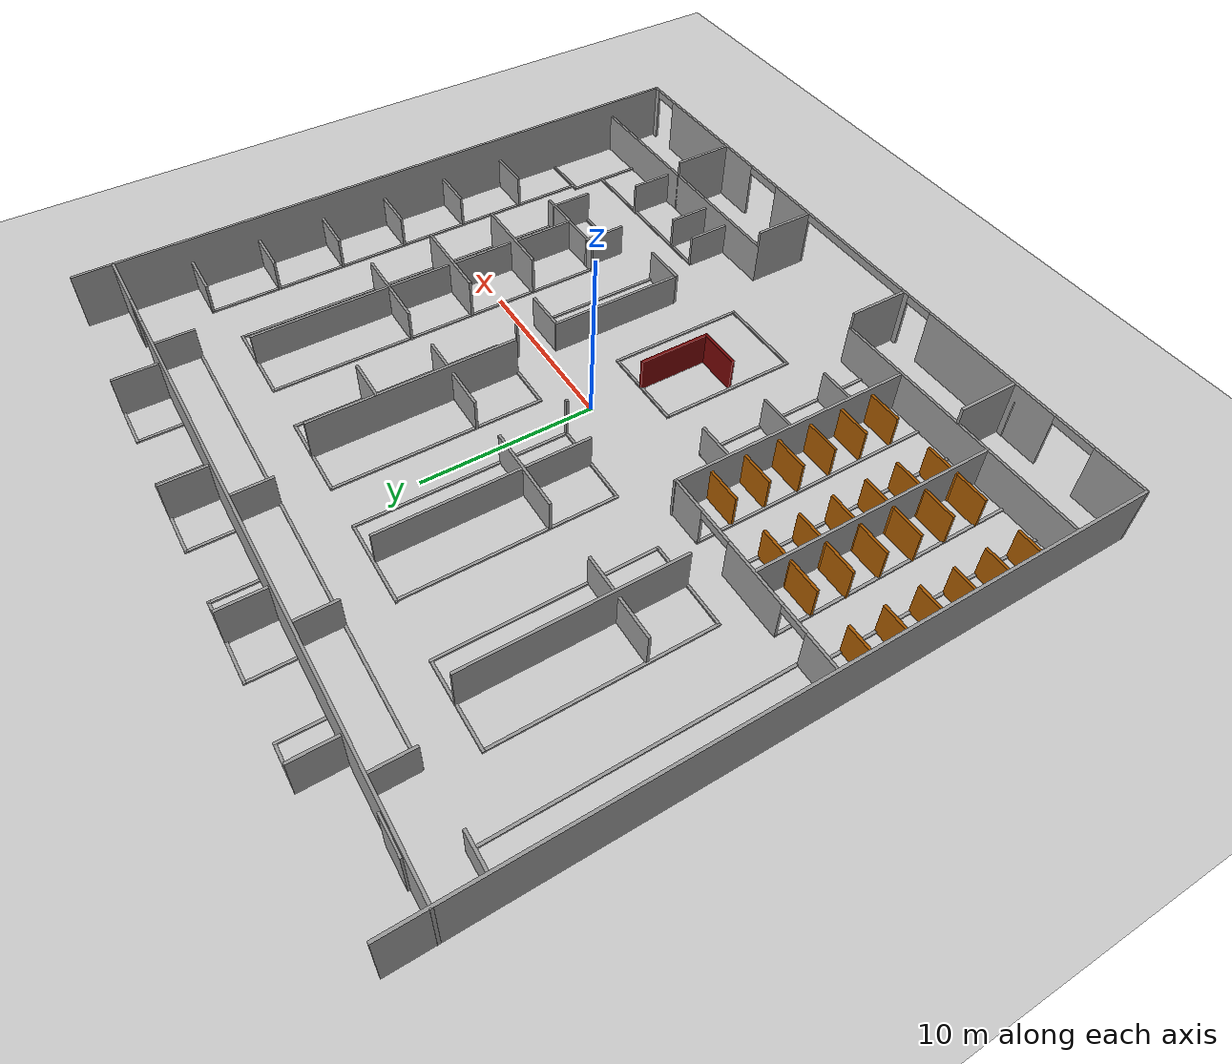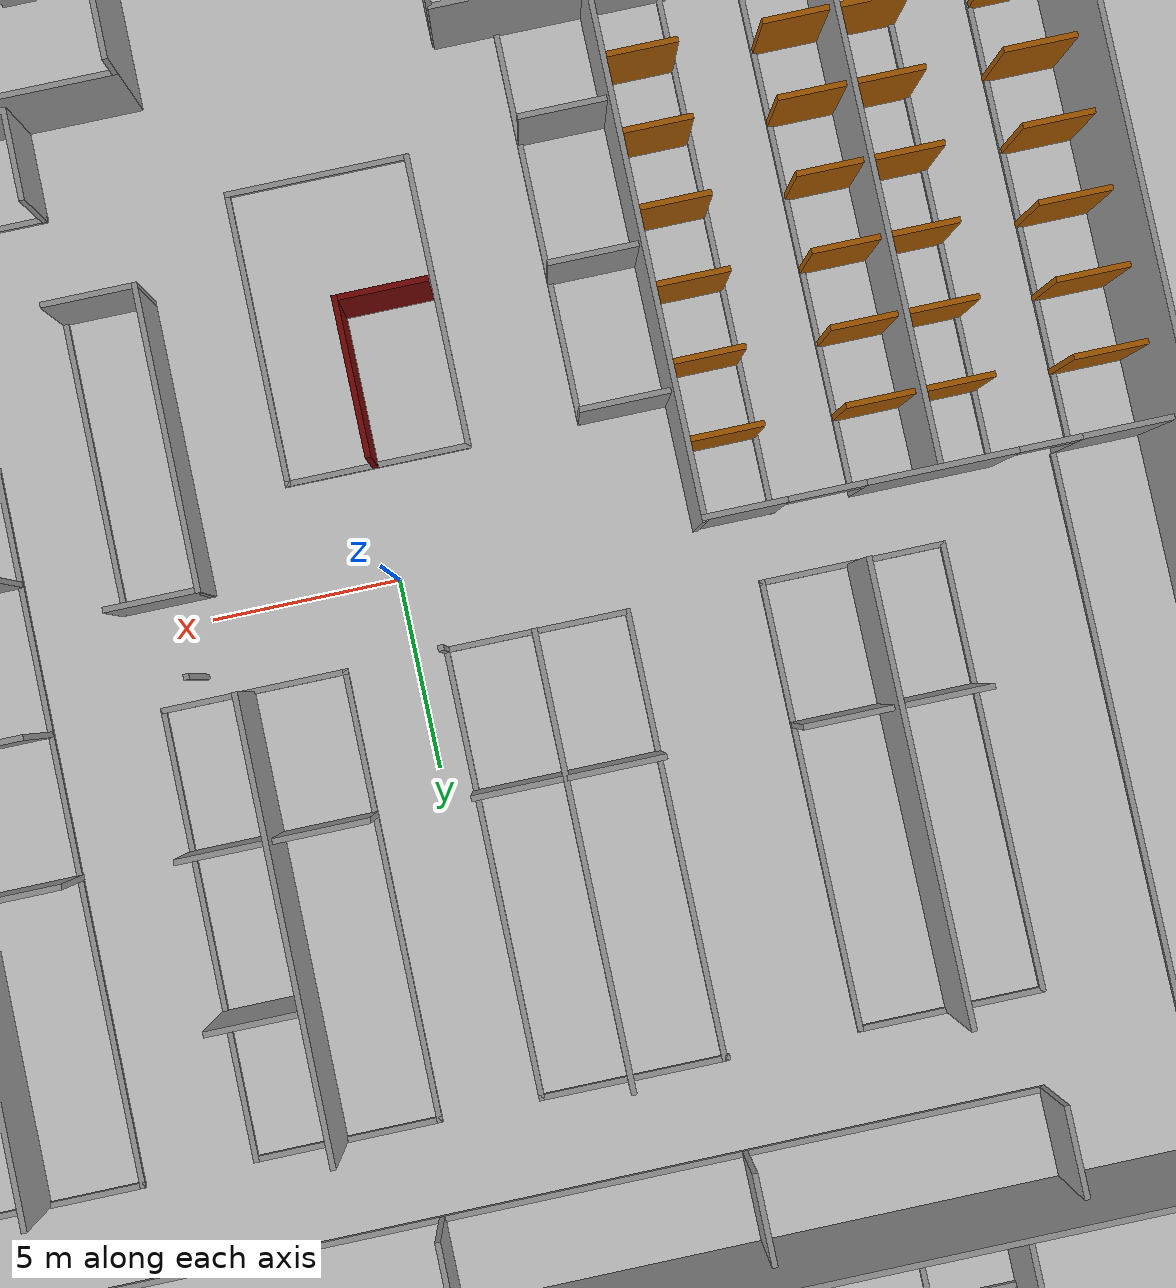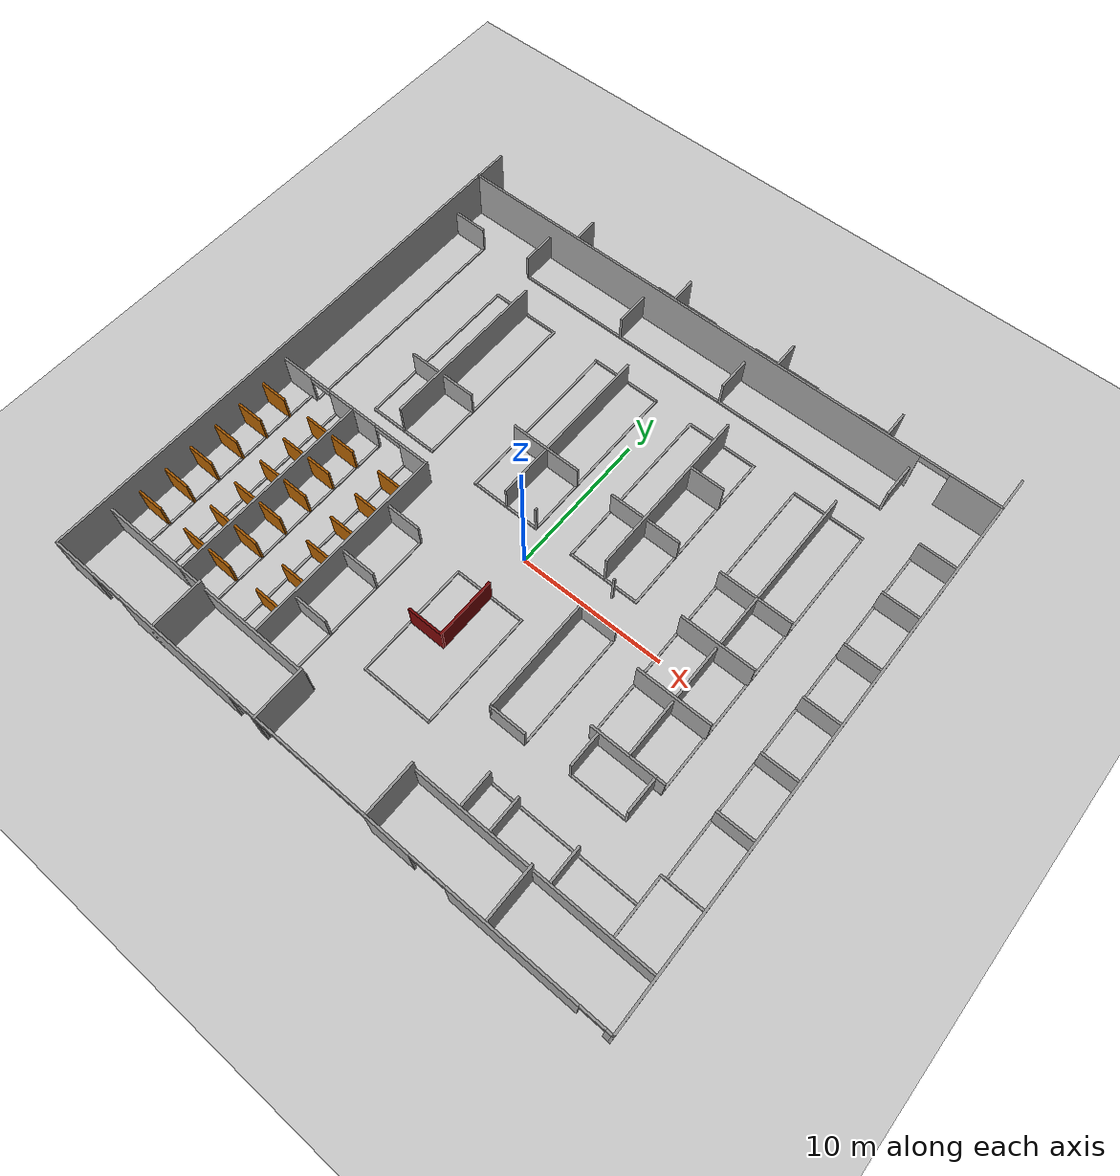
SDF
<sdf version="1.7">
 <world name="default">
  <light name="sun" type="directional">
   <pose>0 0 10 0 -0 0</pose>
   <diffuse>0.8 0.8 0.8 1</diffuse>
   <specular>0.2 0.2 0.2 1</specular>
   <attenuation>
    <range>1000</range>
    <constant>0.9</constant>
    <linear>0.01</linear>
    <quadratic>0.001</quadratic>
   </attenuation>
   <direction>-0.5 0.1 -0.9</direction>
   <spot><inner_angle>0</inner_angle><outer_angle>0</outer_angle><falloff>0</falloff></spot>
  </light>
  <model name="ground_plane">
   <static>1</static>
   <link name="link">
    <collision name="collision">
     <geometry><plane><normal>0 0 1</normal><size>100 100</size></plane></geometry>
     <surface><friction><ode><mu>100</mu><mu2>50</mu2></ode></friction></surface>
    </collision>
    <visual name="visual">
     <cast_shadows>0</cast_shadows>
     <geometry><plane><normal>0 0 1</normal><size>100 100</size></plane></geometry>
     <material>
      <script><uri>file://media/materials/scripts/gazebo.material</uri><name>Gazebo/Grey</name></script>
     </material>
    </visual>
   </link>
  </model>
  <gravity>0 0 -9.8</gravity>
  <magnetic_field>6e-06 2.3e-05 -4.2e-05</magnetic_field>
  <atmosphere type="adiabatic"/>
  <physics type="ode">
   <max_step_size>0.001</max_step_size>
   <real_time_factor>1</real_time_factor>
   <real_time_update_rate>1000</real_time_update_rate>
  </physics>
  <scene><ambient>0.4 0.4 0.4 1</ambient><background>0.7 0.7 0.7 1</background><shadows>1</shadows></scene>
  <audio><device>default</device></audio>
  <spherical_coordinates>
   <surface_model>EARTH_WGS84</surface_model>
   <latitude_deg>0</latitude_deg>
   <longitude_deg>0</longitude_deg>
   <elevation>0</elevation>
   <heading_deg>0</heading_deg>
  </spherical_coordinates>
  <model name="actor0_collision_model">
   <static>false</static>
   <link name="link">
    <collision name="link">
     <pose>0 -0.18 0.00 1.57 0 0</pose>
     <geometry><cylinder><radius>0.3</radius><length>1.8</length></cylinder></geometry>
    </collision>
   </link>
  </model>
  <model name="ATC_hall">
   <pose>0.064513 1.99679 0 0 -0 0</pose>
   <link name="Door_8">
    <collision name="Door_8_Collision">
     <geometry><box><size>2 0.17 3</size></box></geometry>
     <pose>0 0 1.5 0 -0 0</pose>
    </collision>
    <visual name="Door_8_Visual">
     <pose>0 0 1.5 0 -0 0</pose>
     <geometry><box><size>2 0.17 3</size></box></geometry>
     <material>
      <script><uri>file://media/materials/scripts/gazebo.material</uri><name>Gazebo/Grey</name></script>
     </material>
    </visual>
    <pose>-16.713 16.852 0 0 -0 0</pose>
   </link>
   <link name="Wall_11">
    <collision name="Wall_11_Collision">
     <geometry><box><size>0.15 0.15 2.5</size></box></geometry>
     <pose>0 0 1.25 0 -0 0</pose>
    </collision>
    <visual name="Wall_11_Visual">
     <pose>0 0 1.25 0 -0 0</pose>
     <geometry><box><size>0.15 0.15 2.5</size></box></geometry>
     <material>
      <script><uri>file://media/materials/scripts/gazebo.material</uri><name>Gazebo/Grey</name></script>
      <ambient>1 1 1 1</ambient>
     </material>
     <meta><layer>0</layer></meta>
    </visual>
    <pose>-12.273 -19.224 0 0 -0 0</pose>
   </link>
   <link name="Wall_13">
    <collision name="Wall_13_Collision">
     <geometry><box><size>3.5 0.15 3.5</size></box></geometry>
     <pose>0 0 1.75 0 -0 0</pose>
    </collision>
    <visual name="Wall_13_Visual">
     <pose>0 0 1.75 0 -0 0</pose>
     <geometry><box><size>3.5 0.15 3.5</size></box></geometry>
     <material>
      <script><uri>file://media/materials/scripts/gazebo.material</uri><name>Gazebo/Grey</name></script>
      <ambient>0.890196 0.890196 0.890196 1</ambient>
     </material>
     <meta><layer>0</layer></meta>
    </visual>
    <pose>-11.92 -17.41 0 0 -0 1.5708</pose>
   </link>
   <link name="Wall_15">
    <collision name="Wall_15_Collision">
     <geometry><box><size>3.6 0.15 3.5</size></box></geometry>
     <pose>0 0 1.75 0 -0 0</pose>
    </collision>
    <visual name="Wall_15_Visual">
     <pose>0 0 1.75 0 -0 0</pose>
     <geometry><box><size>3.6 0.15 3.5</size></box></geometry>
     <material>
      <script><uri>file://media/materials/scripts/gazebo.material</uri><name>Gazebo/Grey</name></script>
      <ambient>0.890196 0.890196 0.890196 1</ambient>
     </material>
     <meta><layer>0</layer></meta>
    </visual>
    <pose>-3.92 -17.519 0 0 -0 -1.5708</pose>
   </link>
   <link name="Wall_17">
    <collision name="Wall_17_Collision">
     <geometry><box><size>3.5 0.15 3.5</size></box></geometry>
     <pose>0 0 1.75 0 -0 0</pose>
    </collision>
    <visual name="Wall_17_Visual">
     <pose>0 0 1.75 0 -0 0</pose>
     <geometry><box><size>3.5 0.15 3.5</size></box></geometry>
     <material>
      <script><uri>file://media/materials/scripts/gazebo.material</uri><name>Gazebo/Grey</name></script>
      <ambient>0.890196 0.890196 0.890196 1</ambient>
     </material>
     <meta><layer>0</layer></meta>
    </visual>
    <pose>4.08 -17.407 0 0 -0 1.5708</pose>
   </link>
   <link name="Wall_19">
    <collision name="Wall_19_Collision">
     <geometry><box><size>3.5 0.15 3.5</size></box></geometry>
     <pose>0 0 1.75 0 -0 0</pose>
    </collision>
    <visual name="Wall_19_Visual">
     <pose>0 0 1.75 0 -0 0</pose>
     <geometry><box><size>3.5 0.15 3.5</size></box></geometry>
     <material>
      <script><uri>file://media/materials/scripts/gazebo.material</uri><name>Gazebo/Grey</name></script>
      <ambient>0.890196 0.890196 0.890196 1</ambient>
     </material>
     <meta><layer>0</layer></meta>
    </visual>
    <pose>12.08 -17.407 0 0 -0 1.5708</pose>
   </link>
   <link name="Wall_195">
    <collision name="Wall_195_Collision">
     <geometry><box><size>2.5 0.15 2.5</size></box></geometry>
     <pose>0 0 1.25 0 -0 0</pose>
    </collision>
    <visual name="Wall_195_Visual">
     <pose>0 0 1.25 0 -0 0</pose>
     <geometry><box><size>2.5 0.15 2.5</size></box></geometry>
     <material>
      <script><uri>file://media/materials/scripts/gazebo.material</uri><name>Gazebo/Grey</name></script>
      <ambient>0 0 0 1</ambient>
     </material>
     <meta><layer>0</layer></meta>
    </visual>
    <pose>4.08 18.069 0 0 -0 1.5708</pose>
   </link>
   <link name="Wall_199">
    <collision name="Wall_199_Collision">
     <geometry><box><size>16.059 0.15 0.1</size></box></geometry>
     <pose>0 0 0.05 0 -0 0</pose>
    </collision>
    <visual name="Wall_199_Visual">
     <pose>0 0 0.05 0 -0 0</pose>
     <geometry><box><size>16.059 0.15 0.1</size></box></geometry>
     <material>
      <script><uri>file://media/materials/scripts/gazebo.material</uri><name>Gazebo/Grey</name></script>
      <ambient>0.454902 0.454902 0.454902 1</ambient>
     </material>
     <meta><layer>0</layer></meta>
    </visual>
    <pose>-17.5375 6.3535 0 0 -0 -1.57048</pose>
   </link>
   <link name="Wall_2">
    <pose>0.004999 -19.224 0 0 -0 0</pose>
    <visual name="Wall_2_Visual_0">
     <pose>-18.459 0 1.75 0 -0 0</pose>
     <geometry><box><size>3.082 0.15 3.5</size></box></geometry>
     <material>
      <script><uri>file://media/materials/scripts/gazebo.material</uri><name>Gazebo/Grey</name></script>
      <ambient>0.890196 0.890196 0.890196 1</ambient>
     </material>
     <meta><layer>0</layer></meta>
    </visual>
    <collision name="Wall_2_Collision_0">
     <geometry><box><size>3.082 0.15 3.5</size></box></geometry>
     <pose>-18.459 0 1.75 0 -0 0</pose>
    </collision>
    <visual name="Wall_2_Visual_1">
     <pose>-10.213 0 1.75 0 -0 0</pose>
     <geometry><box><size>8.61 0.15 3.5</size></box></geometry>
     <material>
      <script><uri>file://media/materials/scripts/gazebo.material</uri><name>Gazebo/Grey</name></script>
      <ambient>0.890196 0.890196 0.890196 1</ambient>
     </material>
     <meta><layer>0</layer></meta>
    </visual>
    <collision name="Wall_2_Collision_1">
     <geometry><box><size>8.61 0.15 3.5</size></box></geometry>
     <pose>-10.213 0 1.75 0 -0 0</pose>
    </collision>
    <visual name="Wall_2_Visual_2">
     <pose>-4.048 0 1.75 0 -0 0</pose>
     <geometry><box><size>0.519981 0.15 3.5</size></box></geometry>
     <material>
      <script><uri>file://media/materials/scripts/gazebo.material</uri><name>Gazebo/Grey</name></script>
      <ambient>0.890196 0.890196 0.890196 1</ambient>
     </material>
     <meta><layer>0</layer></meta>
    </visual>
    <collision name="Wall_2_Collision_2">
     <geometry><box><size>0.519981 0.15 3.5</size></box></geometry>
     <pose>-4.048 0 1.75 0 -0 0</pose>
    </collision>
    <visual name="Wall_2_Visual_3">
     <pose>5.54699 0 1.75 0 -0 0</pose>
     <geometry><box><size>3.07002 0.15 3.5</size></box></geometry>
     <material>
      <script><uri>file://media/materials/scripts/gazebo.material</uri><name>Gazebo/Grey</name></script>
      <ambient>0.890196 0.890196 0.890196 1</ambient>
     </material>
     <meta><layer>0</layer></meta>
    </visual>
    <collision name="Wall_2_Collision_3">
     <geometry><box><size>3.07002 0.15 3.5</size></box></geometry>
     <pose>5.54699 0 1.75 0 -0 0</pose>
    </collision>
    <visual name="Wall_2_Visual_4">
     <pose>13.6861 0 1.75 0 -0 0</pose>
     <geometry><box><size>8.40819 0.15 3.5</size></box></geometry>
     <material>
      <script><uri>file://media/materials/scripts/gazebo.material</uri><name>Gazebo/Grey</name></script>
      <ambient>0.890196 0.890196 0.890196 1</ambient>
     </material>
     <meta><layer>0</layer></meta>
    </visual>
    <collision name="Wall_2_Collision_4">
     <geometry><box><size>8.40819 0.15 3.5</size></box></geometry>
     <pose>13.6861 0 1.75 0 -0 0</pose>
    </collision>
    <visual name="Wall_2_Visual_5">
     <pose>19.7451 0 1.75 0 -0 0</pose>
     <geometry><box><size>0.509814 0.15 3.5</size></box></geometry>
     <material>
      <script><uri>file://media/materials/scripts/gazebo.material</uri><name>Gazebo/Grey</name></script>
      <ambient>0.890196 0.890196 0.890196 1</ambient>
     </material>
     <meta><layer>0</layer></meta>
    </visual>
    <collision name="Wall_2_Collision_5">
     <geometry><box><size>0.509814 0.15 3.5</size></box></geometry>
     <pose>19.7451 0 1.75 0 -0 0</pose>
    </collision>
    <visual name="Wall_2_Visual_6">
     <pose>-15.718 0 3.25 0 -0 0</pose>
     <geometry><box><size>2.4 0.15 0.5</size></box></geometry>
     <material>
      <script><uri>file://media/materials/scripts/gazebo.material</uri><name>Gazebo/Grey</name></script>
      <ambient>0.890196 0.890196 0.890196 1</ambient>
     </material>
     <meta><layer>0</layer></meta>
    </visual>
    <collision name="Wall_2_Collision_6">
     <geometry><box><size>2.4 0.15 0.5</size></box></geometry>
     <pose>-15.718 0 3.25 0 -0 0</pose>
    </collision>
    <visual name="Wall_2_Visual_7">
     <pose>-5.108 0 3.25 0 -0 0</pose>
     <geometry><box><size>1.6 0.15 0.5</size></box></geometry>
     <material>
      <script><uri>file://media/materials/scripts/gazebo.material</uri><name>Gazebo/Grey</name></script>
      <ambient>0.890196 0.890196 0.890196 1</ambient>
     </material>
     <meta><layer>0</layer></meta>
    </visual>
    <collision name="Wall_2_Collision_7">
     <geometry><box><size>1.6 0.15 0.5</size></box></geometry>
     <pose>-5.108 0 3.25 0 -0 0</pose>
    </collision>
    <visual name="Wall_2_Visual_8">
     <pose>0.111985 0 3.25 0 -0 0</pose>
     <geometry><box><size>7.8 0.15 0.5</size></box></geometry>
     <material>
      <script><uri>file://media/materials/scripts/gazebo.material</uri><name>Gazebo/Grey</name></script>
      <ambient>0.890196 0.890196 0.890196 1</ambient>
     </material>
     <meta><layer>0</layer></meta>
    </visual>
    <collision name="Wall_2_Collision_8">
     <geometry><box><size>7.8 0.15 0.5</size></box></geometry>
     <pose>0.111985 0 3.25 0 -0 0</pose>
    </collision>
    <visual name="Wall_2_Visual_9">
     <pose>8.282 0 3.25 0 -0 0</pose>
     <geometry><box><size>2.4 0.15 0.5</size></box></geometry>
     <material>
      <script><uri>file://media/materials/scripts/gazebo.material</uri><name>Gazebo/Grey</name></script>
      <ambient>0.890196 0.890196 0.890196 1</ambient>
     </material>
     <meta><layer>0</layer></meta>
    </visual>
    <collision name="Wall_2_Collision_9">
     <geometry><box><size>2.4 0.15 0.5</size></box></geometry>
     <pose>8.282 0 3.25 0 -0 0</pose>
    </collision>
    <visual name="Wall_2_Visual_10">
     <pose>18.6902 0 3.25 0 -0 0</pose>
     <geometry><box><size>1.6 0.15 0.5</size></box></geometry>
     <material>
      <script><uri>file://media/materials/scripts/gazebo.material</uri><name>Gazebo/Grey</name></script>
      <ambient>0.890196 0.890196 0.890196 1</ambient>
     </material>
     <meta><layer>0</layer></meta>
    </visual>
    <collision name="Wall_2_Collision_10">
     <geometry><box><size>1.6 0.15 0.5</size></box></geometry>
     <pose>18.6902 0 3.25 0 -0 0</pose>
    </collision>
   </link>
   <link name="Wall_204">
    <collision name="Wall_204_Collision">
     <geometry><box><size>14 0.15 0.1</size></box></geometry>
     <pose>0 0 0.05 0 -0 0</pose>
    </collision>
    <visual name="Wall_204_Visual">
     <pose>0 0 0.05 0 -0 0</pose>
     <geometry><box><size>14 0.15 0.1</size></box></geometry>
     <material>
      <script><uri>file://media/materials/scripts/gazebo.material</uri><name>Gazebo/Grey</name></script>
      <ambient>0.462745 0.462745 0.462745 1</ambient>
     </material>
     <meta><layer>0</layer></meta>
    </visual>
    <pose>-18.002 -8.696 0 0 -0 -1.5708</pose>
   </link>
   <link name="Wall_206">
    <collision name="Wall_206_Collision">
     <geometry><box><size>14 0.15 0.1</size></box></geometry>
     <pose>0 0 0.05 0 -0 0</pose>
    </collision>
    <visual name="Wall_206_Visual">
     <pose>0 0 0.05 0 -0 0</pose>
     <geometry><box><size>14 0.15 0.1</size></box></geometry>
     <material>
      <script><uri>file://media/materials/scripts/gazebo.material</uri><name>Gazebo/Grey</name></script>
      <ambient>0.462745 0.462745 0.462745 1</ambient>
     </material>
     <meta><layer>0</layer></meta>
    </visual>
    <pose>-15.864 -8.685 0 0 -0 -1.5708</pose>
   </link>
   <link name="Wall_208">
    <collision name="Wall_208_Collision">
     <geometry><box><size>14 0.15 0.1</size></box></geometry>
     <pose>0 0 0.05 0 -0 0</pose>
    </collision>
    <visual name="Wall_208_Visual">
     <pose>0 0 0.05 0 -0 0</pose>
     <geometry><box><size>14 0.15 0.1</size></box></geometry>
     <material>
      <script><uri>file://media/materials/scripts/gazebo.material</uri><name>Gazebo/Grey</name></script>
      <ambient>0.462745 0.462745 0.462745 1</ambient>
     </material>
     <meta><layer>0</layer></meta>
    </visual>
    <pose>-12.133 -8.708 0 0 -0 -1.5708</pose>
   </link>
   <link name="Wall_21">
    <collision name="Wall_21_Collision">
     <geometry><box><size>16.1 0.15 2.5</size></box></geometry>
     <pose>0 0 1.25 0 -0 0</pose>
    </collision>
    <visual name="Wall_21_Visual">
     <pose>0 0 1.25 0 -0 0</pose>
     <geometry><box><size>16.1 0.15 2.5</size></box></geometry>
     <material>
      <script><uri>file://media/materials/scripts/gazebo.material</uri><name>Gazebo/Grey</name></script>
      <ambient>0.890196 0.890196 0.890196 1</ambient>
     </material>
     <meta><layer>0</layer></meta>
    </visual>
    <pose>-11.934 -15.713 0 0 -0 0</pose>
   </link>
   <link name="Wall_211">
    <collision name="Wall_211_Collision">
     <geometry><box><size>14 0.15 0.1</size></box></geometry>
     <pose>0 0 0.05 0 -0 0</pose>
    </collision>
    <visual name="Wall_211_Visual">
     <pose>0 0 0.05 0 -0 0</pose>
     <geometry><box><size>14 0.15 0.1</size></box></geometry>
     <material>
      <script><uri>file://media/materials/scripts/gazebo.material</uri><name>Gazebo/Grey</name></script>
      <ambient>0.462745 0.462745 0.462745 1</ambient>
     </material>
     <meta><layer>0</layer></meta>
    </visual>
    <pose>-9.981 -8.67 0 0 -0 -1.5708</pose>
   </link>
   <link name="Wall_213">
    <collision name="Wall_213_Collision">
     <geometry><box><size>2.5 0.15 0.1</size></box></geometry>
     <pose>0 0 0.05 0 -0 0</pose>
    </collision>
    <visual name="Wall_213_Visual">
     <pose>0 0 0.05 0 -0 0</pose>
     <geometry><box><size>2.5 0.15 0.1</size></box></geometry>
     <material>
      <script><uri>file://media/materials/scripts/gazebo.material</uri><name>Gazebo/Grey</name></script>
      <ambient>0.454902 0.454902 0.454902 1</ambient>
     </material>
     <meta><layer>0</layer></meta>
    </visual>
    <pose>-10.745 19.117 0 0 -0 0</pose>
   </link>
   <link name="Wall_216">
    <collision name="Wall_216_Collision">
     <geometry><box><size>2.5 0.15 0.1</size></box></geometry>
     <pose>0 0 0.05 0 -0 0</pose>
    </collision>
    <visual name="Wall_216_Visual">
     <pose>0 0 0.05 0 -0 0</pose>
     <geometry><box><size>2.5 0.15 0.1</size></box></geometry>
     <material>
      <script><uri>file://media/materials/scripts/gazebo.material</uri><name>Gazebo/Grey</name></script>
      <ambient>0.454902 0.454902 0.454902 1</ambient>
     </material>
     <meta><layer>0</layer></meta>
    </visual>
    <pose>-9.57 17.942 0 0 -0 -1.5708</pose>
   </link>
   <link name="Wall_220">
    <collision name="Wall_220_Collision">
     <geometry><box><size>2.5 0.15 0.1</size></box></geometry>
     <pose>0 0 0.05 0 -0 0</pose>
    </collision>
    <visual name="Wall_220_Visual">
     <pose>0 0 0.05 0 -0 0</pose>
     <geometry><box><size>2.5 0.15 0.1</size></box></geometry>
     <material>
      <script><uri>file://media/materials/scripts/gazebo.material</uri><name>Gazebo/Grey</name></script>
      <ambient>0.462745 0.462745 0.462745 1</ambient>
     </material>
     <meta><layer>0</layer></meta>
    </visual>
    <pose>-5.095 19.238 0 0 -0 3.14159</pose>
   </link>
   <link name="Wall_222">
    <collision name="Wall_222_Collision">
     <geometry><box><size>2.5 0.15 0.1</size></box></geometry>
     <pose>0 0 0.05 0 -0 0</pose>
    </collision>
    <visual name="Wall_222_Visual">
     <pose>0 0 0.05 0 -0 0</pose>
     <geometry><box><size>2.5 0.15 0.1</size></box></geometry>
     <material>
      <script><uri>file://media/materials/scripts/gazebo.material</uri><name>Gazebo/Grey</name></script>
      <ambient>0.454902 0.454902 0.454902 1</ambient>
     </material>
     <meta><layer>0</layer></meta>
    </visual>
    <pose>-6.27 18.063 0 0 -0 -1.5708</pose>
   </link>
   <link name="Wall_224">
    <collision name="Wall_224_Collision">
     <geometry><box><size>2.5 0.15 0.1</size></box></geometry>
     <pose>0 0 0.05 0 -0 0</pose>
    </collision>
    <visual name="Wall_224_Visual">
     <pose>0 0 0.05 0 -0 0</pose>
     <geometry><box><size>2.5 0.15 0.1</size></box></geometry>
     <material>
      <script><uri>file://media/materials/scripts/gazebo.material</uri><name>Gazebo/Grey</name></script>
      <ambient>0.462745 0.462745 0.462745 1</ambient>
     </material>
     <meta><layer>0</layer></meta>
    </visual>
    <pose>-2.745 19.238 0 0 -0 0</pose>
   </link>
   <link name="Wall_226">
    <collision name="Wall_226_Collision">
     <geometry><box><size>2.5 0.15 0.1</size></box></geometry>
     <pose>0 0 0.05 0 -0 0</pose>
    </collision>
    <visual name="Wall_226_Visual">
     <pose>0 0 0.05 0 -0 0</pose>
     <geometry><box><size>2.5 0.15 0.1</size></box></geometry>
     <material>
      <script><uri>file://media/materials/scripts/gazebo.material</uri><name>Gazebo/Grey</name></script>
      <ambient>0.462745 0.462745 0.462745 1</ambient>
     </material>
     <meta><layer>0</layer></meta>
    </visual>
    <pose>-1.57 18.063 0 0 -0 -1.5708</pose>
   </link>
   <link name="Wall_228">
    <collision name="Wall_228_Collision">
     <geometry><box><size>2.5 0.15 0.1</size></box></geometry>
     <pose>0 0 0.05 0 -0 0</pose>
    </collision>
    <visual name="Wall_228_Visual">
     <pose>0 0 0.05 0 -0 0</pose>
     <geometry><box><size>2.5 0.15 0.1</size></box></geometry>
     <material>
      <script><uri>file://media/materials/scripts/gazebo.material</uri><name>Gazebo/Grey</name></script>
      <ambient>0.462745 0.462745 0.462745 1</ambient>
     </material>
     <meta><layer>0</layer></meta>
    </visual>
    <pose>2.905 19.244 0 0 -0 3.14159</pose>
   </link>
   <link name="Wall_23">
    <collision name="Wall_23_Collision">
     <geometry><box><size>16 0.15 2.5</size></box></geometry>
     <pose>0 0 1.25 0 -0 0</pose>
    </collision>
    <visual name="Wall_23_Visual">
     <pose>0 0 1.25 0 -0 0</pose>
     <geometry><box><size>16 0.15 2.5</size></box></geometry>
     <material>
      <script><uri>file://media/materials/scripts/gazebo.material</uri><name>Gazebo/Grey</name></script>
      <ambient>0.890196 0.890196 0.890196 1</ambient>
     </material>
     <meta><layer>0</layer></meta>
    </visual>
    <pose>12.005 -15.732 0 0 -0 0</pose>
   </link>
   <link name="Wall_230">
    <collision name="Wall_230_Collision">
     <geometry><box><size>2.5 0.15 0.1</size></box></geometry>
     <pose>0 0 0.05 0 -0 0</pose>
    </collision>
    <visual name="Wall_230_Visual">
     <pose>0 0 0.05 0 -0 0</pose>
     <geometry><box><size>2.5 0.15 0.1</size></box></geometry>
     <material>
      <script><uri>file://media/materials/scripts/gazebo.material</uri><name>Gazebo/Grey</name></script>
      <ambient>0.462745 0.462745 0.462745 1</ambient>
     </material>
     <meta><layer>0</layer></meta>
    </visual>
    <pose>1.73 18.069 0 0 -0 -1.5708</pose>
   </link>
   <link name="Wall_232">
    <collision name="Wall_232_Collision">
     <geometry><box><size>2.5 0.15 0.1</size></box></geometry>
     <pose>0 0 0.05 0 -0 0</pose>
    </collision>
    <visual name="Wall_232_Visual">
     <pose>0 0 0.05 0 -0 0</pose>
     <geometry><box><size>2.5 0.15 0.1</size></box></geometry>
     <material>
      <script><uri>file://media/materials/scripts/gazebo.material</uri><name>Gazebo/Grey</name></script>
      <ambient>0.454902 0.454902 0.454902 1</ambient>
     </material>
     <meta><layer>0</layer></meta>
    </visual>
    <pose>5.255 19.244 0 0 -0 0</pose>
   </link>
   <link name="Wall_234">
    <collision name="Wall_234_Collision">
     <geometry><box><size>2.5 0.15 0.1</size></box></geometry>
     <pose>0 0 0.05 0 -0 0</pose>
    </collision>
    <visual name="Wall_234_Visual">
     <pose>0 0 0.05 0 -0 0</pose>
     <geometry><box><size>2.5 0.15 0.1</size></box></geometry>
     <material>
      <script><uri>file://media/materials/scripts/gazebo.material</uri><name>Gazebo/Grey</name></script>
      <ambient>0.454902 0.454902 0.454902 1</ambient>
     </material>
     <meta><layer>0</layer></meta>
    </visual>
    <pose>6.43 18.069 0 0 -0 -1.5708</pose>
   </link>
   <link name="Wall_236">
    <collision name="Wall_236_Collision">
     <geometry><box><size>2.5 0.15 0.1</size></box></geometry>
     <pose>0 0 0.05 0 -0 0</pose>
    </collision>
    <visual name="Wall_236_Visual">
     <pose>0 0 0.05 0 -0 0</pose>
     <geometry><box><size>2.5 0.15 0.1</size></box></geometry>
     <material>
      <script><uri>file://media/materials/scripts/gazebo.material</uri><name>Gazebo/Grey</name></script>
      <ambient>0.454902 0.454902 0.454902 1</ambient>
     </material>
     <meta><layer>0</layer></meta>
    </visual>
    <pose>10.905 19.238 0 0 -0 3.14159</pose>
   </link>
   <link name="Wall_238">
    <collision name="Wall_238_Collision">
     <geometry><box><size>2.5 0.15 0.1</size></box></geometry>
     <pose>0 0 0.05 0 -0 0</pose>
    </collision>
    <visual name="Wall_238_Visual">
     <pose>0 0 0.05 0 -0 0</pose>
     <geometry><box><size>2.5 0.15 0.1</size></box></geometry>
     <material>
      <script><uri>file://media/materials/scripts/gazebo.material</uri><name>Gazebo/Grey</name></script>
      <ambient>0.454902 0.454902 0.454902 1</ambient>
     </material>
     <meta><layer>0</layer></meta>
    </visual>
    <pose>9.73 18.063 0 0 -0 -1.5708</pose>
   </link>
   <link name="Wall_25">
    <collision name="Wall_25_Collision">
     <geometry><box><size>14.0341 0.15 2.5</size></box></geometry>
     <pose>0 0 1.25 0 -0 0</pose>
    </collision>
    <visual name="Wall_25_Visual">
     <pose>0 0 1.25 0 -0 0</pose>
     <geometry><box><size>14.0341 0.15 2.5</size></box></geometry>
     <material>
      <script><uri>file://media/materials/scripts/gazebo.material</uri><name>Gazebo/Grey</name></script>
      <ambient>0.890196 0.890196 0.890196 1</ambient>
     </material>
     <meta><layer>0</layer></meta>
    </visual>
    <pose>-7.92273 -8.65395 0 0 -0 1.57119</pose>
   </link>
   <link name="Wall_27">
    <pose>-13.8505 -1.75145 0 0 -0 3.14159</pose>
    <visual name="Wall_27_Visual_0">
     <pose>-4.90273 0 1.25 0 -0 0</pose>
     <geometry><box><size>2.19455 0.15 2.5</size></box></geometry>
     <material>
      <script><uri>file://media/materials/scripts/gazebo.material</uri><name>Gazebo/Grey</name></script>
      <ambient>0.890196 0.890196 0.890196 1</ambient>
     </material>
     <meta><layer>0</layer></meta>
    </visual>
    <collision name="Wall_27_Collision_0">
     <geometry><box><size>2.19455 0.15 2.5</size></box></geometry>
     <pose>-4.90273 0 1.25 0 -0 0</pose>
    </collision>
    <visual name="Wall_27_Visual_1">
     <pose>0.128549 0 1.25 0 -0 0</pose>
     <geometry><box><size>3.868 0.15 2.5</size></box></geometry>
     <material>
      <script><uri>file://media/materials/scripts/gazebo.material</uri><name>Gazebo/Grey</name></script>
      <ambient>0.890196 0.890196 0.890196 1</ambient>
     </material>
     <meta><layer>0</layer></meta>
    </visual>
    <collision name="Wall_27_Collision_1">
     <geometry><box><size>3.868 0.15 2.5</size></box></geometry>
     <pose>0.128549 0 1.25 0 -0 0</pose>
    </collision>
    <visual name="Wall_27_Visual_2">
     <pose>4.83127 0 1.25 0 -0 0</pose>
     <geometry><box><size>2.33745 0.15 2.5</size></box></geometry>
     <material>
      <script><uri>file://media/materials/scripts/gazebo.material</uri><name>Gazebo/Grey</name></script>
      <ambient>0.890196 0.890196 0.890196 1</ambient>
     </material>
     <meta><layer>0</layer></meta>
    </visual>
    <collision name="Wall_27_Collision_2">
     <geometry><box><size>2.33745 0.15 2.5</size></box></geometry>
     <pose>4.83127 0 1.25 0 -0 0</pose>
    </collision>
    <visual name="Wall_27_Visual_3">
     <pose>-2.80545 0 2.25 0 -0 0</pose>
     <geometry><box><size>2 0.15 0.5</size></box></geometry>
     <material>
      <script><uri>file://media/materials/scripts/gazebo.material</uri><name>Gazebo/Grey</name></script>
      <ambient>0.890196 0.890196 0.890196 1</ambient>
     </material>
     <meta><layer>0</layer></meta>
    </visual>
    <collision name="Wall_27_Collision_3">
     <geometry><box><size>2 0.15 0.5</size></box></geometry>
     <pose>-2.80545 0 2.25 0 -0 0</pose>
    </collision>
    <visual name="Wall_27_Visual_4">
     <pose>2.86255 0 2.25 0 -0 0</pose>
     <geometry><box><size>1.6 0.15 0.5</size></box></geometry>
     <material>
      <script><uri>file://media/materials/scripts/gazebo.material</uri><name>Gazebo/Grey</name></script>
      <ambient>0.890196 0.890196 0.890196 1</ambient>
     </material>
     <meta><layer>0</layer></meta>
    </visual>
    <collision name="Wall_27_Collision_4">
     <geometry><box><size>1.6 0.15 0.5</size></box></geometry>
     <pose>2.86255 0 2.25 0 -0 0</pose>
    </collision>
   </link>
   <link name="Wall_29">
    <collision name="Wall_29_Collision">
     <geometry><box><size>14 0.15 2.5</size></box></geometry>
     <pose>0 0 1.25 0 -0 0</pose>
    </collision>
    <visual name="Wall_29_Visual">
     <pose>0 0 1.25 0 -0 0</pose>
     <geometry><box><size>14 0.15 2.5</size></box></geometry>
     <material>
      <script><uri>file://media/materials/scripts/gazebo.material</uri><name>Gazebo/Grey</name></script>
      <ambient>0.890196 0.890196 0.890196 1</ambient>
     </material>
     <meta><layer>0</layer></meta>
    </visual>
    <pose>-13.92 -8.791 0 0 -0 1.5708</pose>
   </link>
   <link name="Wall_306">
    <collision name="Wall_306_Collision">
     <geometry><box><size>2.5 0.15 2</size></box></geometry>
     <pose>0 0 1 0 -0 0</pose>
    </collision>
    <visual name="Wall_306_Visual">
     <pose>0 0 1 0 -0 0</pose>
     <geometry><box><size>2.5 0.15 2</size></box></geometry>
     <material>
      <script><uri>file://media/materials/scripts/gazebo.material</uri><name>Gazebo/Grey</name></script>
      <ambient>0 0 0 1</ambient>
     </material>
     <meta><layer>0</layer></meta>
    </visual>
    <pose>-13.62 15.573 0 0 -0 -1.5708</pose>
   </link>
   <link name="Wall_308">
    <collision name="Wall_308_Collision">
     <geometry><box><size>28 0.15 0.1</size></box></geometry>
     <pose>0 0 0.05 0 -0 0</pose>
    </collision>
    <visual name="Wall_308_Visual">
     <pose>0 0 0.05 0 -0 0</pose>
     <geometry><box><size>28 0.15 0.1</size></box></geometry>
     <material>
      <script><uri>file://media/materials/scripts/gazebo.material</uri><name>Gazebo/Grey</name></script>
      <ambient>0.454902 0.454902 0.454902 1</ambient>
     </material>
     <meta><layer>0</layer></meta>
    </visual>
    <pose>0.304999 14.394 0 0 -0 -0.000287</pose>
   </link>
   <link name="Wall_310">
    <collision name="Wall_310_Collision">
     <geometry><box><size>2.5 0.15 2</size></box></geometry>
     <pose>0 0 1 0 -0 0</pose>
    </collision>
    <visual name="Wall_310_Visual">
     <pose>0 0 1 0 -0 0</pose>
     <geometry><box><size>2.5 0.15 2</size></box></geometry>
     <material>
      <script><uri>file://media/materials/scripts/gazebo.material</uri><name>Gazebo/Grey</name></script>
      <ambient>0 0 0 1</ambient>
     </material>
     <meta><layer>0</layer></meta>
    </visual>
    <pose>-5.735 15.573 0 0 -0 -1.5708</pose>
   </link>
   <link name="Wall_314">
    <collision name="Wall_314_Collision">
     <geometry><box><size>2.5 0.15 2</size></box></geometry>
     <pose>0 0 1 0 -0 0</pose>
    </collision>
    <visual name="Wall_314_Visual">
     <pose>0 0 1 0 -0 0</pose>
     <geometry><box><size>2.5 0.15 2</size></box></geometry>
     <material>
      <script><uri>file://media/materials/scripts/gazebo.material</uri><name>Gazebo/Grey</name></script>
      <ambient>0 0 0 1</ambient>
     </material>
     <meta><layer>0</layer></meta>
    </visual>
    <pose>2.263 15.573 0 0 -0 -1.5708</pose>
   </link>
   <link name="Wall_323">
    <collision name="Wall_323_Collision">
     <geometry><box><size>2.5 0.15 2</size></box></geometry>
     <pose>0 0 1 0 -0 0</pose>
    </collision>
    <visual name="Wall_323_Visual">
     <pose>0 0 1 0 -0 0</pose>
     <geometry><box><size>2.5 0.15 2</size></box></geometry>
     <material>
      <script><uri>file://media/materials/scripts/gazebo.material</uri><name>Gazebo/Grey</name></script>
      <ambient>0 0 0 1</ambient>
     </material>
     <meta><layer>0</layer></meta>
    </visual>
    <pose>14.237 15.565 0 0 -0 -1.57675</pose>
   </link>
   <link name="Wall_325">
    <collision name="Wall_325_Collision">
     <geometry><box><size>0.15 0.15 0.1</size></box></geometry>
     <pose>0 0 0.05 0 -0 0</pose>
    </collision>
    <visual name="Wall_325_Visual">
     <pose>0 0 0.05 0 -0 0</pose>
     <geometry><box><size>0.15 0.15 0.1</size></box></geometry>
     <material>
      <script><uri>file://media/materials/scripts/gazebo.material</uri><name>Gazebo/Grey</name></script>
      <ambient>1 1 1 1</ambient>
     </material>
     <meta><layer>0</layer></meta>
    </visual>
    <pose>-5.803 11.898 0 0 -0 0</pose>
   </link>
   <link name="Wall_327">
    <collision name="Wall_327_Collision">
     <geometry><box><size>12 0.15 0.1</size></box></geometry>
     <pose>0 0 0.05 0 -0 0</pose>
    </collision>
    <visual name="Wall_327_Visual">
     <pose>0 0 0.05 0 -0 0</pose>
     <geometry><box><size>12 0.15 0.1</size></box></geometry>
     <material>
      <script><uri>file://media/materials/scripts/gazebo.material</uri><name>Gazebo/Grey</name></script>
      <ambient>0.454902 0.454902 0.454902 1</ambient>
     </material>
     <meta><layer>0</layer></meta>
    </visual>
    <pose>-5.735 5.973 0 0 -0 -1.5708</pose>
   </link>
   <link name="Wall_329">
    <collision name="Wall_329_Collision">
     <geometry><box><size>5 0.15 0.1</size></box></geometry>
     <pose>0 0 0.05 0 -0 0</pose>
    </collision>
    <visual name="Wall_329_Visual">
     <pose>0 0 0.05 0 -0 0</pose>
     <geometry><box><size>5 0.15 0.1</size></box></geometry>
     <material>
      <script><uri>file://media/materials/scripts/gazebo.material</uri><name>Gazebo/Grey</name></script>
      <ambient>0.454902 0.454902 0.454902 1</ambient>
     </material>
     <meta><layer>0</layer></meta>
    </visual>
    <pose>-3.31 11.893 0 0 -0 -0.002062</pose>
   </link>
   <link name="Wall_33">
    <collision name="Wall_33_Collision">
     <geometry><box><size>2 0.15 2</size></box></geometry>
     <pose>0 0 1 0 -0 0</pose>
    </collision>
    <visual name="Wall_33_Visual">
     <pose>0 0 1 0 -0 0</pose>
     <geometry><box><size>2 0.15 2</size></box></geometry>
     <material>
      <script><uri>file://media/materials/scripts/gazebo.material</uri><name>Gazebo/Grey</name></script>
      <ambient>0.666667 0.356863 0 1</ambient>
     </material>
     <meta><layer>0</layer></meta>
    </visual>
    <pose>-18.965 -13.791 0 0 -0 0</pose>
   </link>
   <link name="Wall_331">
    <collision name="Wall_331_Collision">
     <geometry><box><size>12 0.15 0.1</size></box></geometry>
     <pose>0 0 0.05 0 -0 0</pose>
    </collision>
    <visual name="Wall_331_Visual">
     <pose>0 0 0.05 0 -0 0</pose>
     <geometry><box><size>12 0.15 0.1</size></box></geometry>
     <material>
      <script><uri>file://media/materials/scripts/gazebo.material</uri><name>Gazebo/Grey</name></script>
      <ambient>0.454902 0.454902 0.454902 1</ambient>
     </material>
     <meta><layer>0</layer></meta>
    </visual>
    <pose>-0.885001 5.963 0 0 -0 -1.5708</pose>
   </link>
   <link name="Wall_332">
    <collision name="Wall_332_Collision">
     <geometry><box><size>0.15 0.15 2.5</size></box></geometry>
     <pose>0 0 1.25 0 -0 0</pose>
    </collision>
    <visual name="Wall_332_Visual">
     <pose>0 0 1.25 0 -0 0</pose>
     <geometry><box><size>0.15 0.15 2.5</size></box></geometry>
     <material>
      <script><uri>file://media/materials/scripts/gazebo.material</uri><name>Gazebo/Grey</name></script>
      <ambient>1 1 1 1</ambient>
     </material>
     <meta><layer>0</layer></meta>
    </visual>
    <pose>-0.885001 0.037999 0 0 -0 0</pose>
   </link>
   <link name="Wall_334">
    <collision name="Wall_334_Collision">
     <geometry><box><size>5 0.15 0.1</size></box></geometry>
     <pose>0 0 0.05 0 -0 0</pose>
    </collision>
    <visual name="Wall_334_Visual">
     <pose>0 0 0.05 0 -0 0</pose>
     <geometry><box><size>5 0.15 0.1</size></box></geometry>
     <material>
      <script><uri>file://media/materials/scripts/gazebo.material</uri><name>Gazebo/Grey</name></script>
      <ambient>0.454902 0.454902 0.454902 1</ambient>
     </material>
     <meta><layer>0</layer></meta>
    </visual>
    <pose>-3.31 0.042999 0 0 -0 3.13953</pose>
   </link>
   <link name="Wall_336">
    <collision name="Wall_336_Collision">
     <geometry><box><size>11.8 0.15 2</size></box></geometry>
     <pose>0 0 1 0 -0 0</pose>
    </collision>
    <visual name="Wall_336_Visual">
     <pose>0 0 1 0 -0 0</pose>
     <geometry><box><size>11.8 0.15 2</size></box></geometry>
     <material>
      <script><uri>file://media/materials/scripts/gazebo.material</uri><name>Gazebo/Grey</name></script>
      <ambient>0 0 0 1</ambient>
     </material>
     <meta><layer>0</layer></meta>
    </visual>
    <pose>-3.235 5.932 0 0 -0 -1.5708</pose>
   </link>
   <link name="Wall_338">
    <collision name="Wall_338_Collision">
     <geometry><box><size>5 0.15 2</size></box></geometry>
     <pose>0 0 1 0 -0 0</pose>
    </collision>
    <visual name="Wall_338_Visual">
     <pose>0 0 1 0 -0 0</pose>
     <geometry><box><size>5 0.15 2</size></box></geometry>
     <material>
      <script><uri>file://media/materials/scripts/gazebo.material</uri><name>Gazebo/Grey</name></script>
      <ambient>0 0 0 1</ambient>
     </material>
     <meta><layer>0</layer></meta>
    </visual>
    <pose>-3.31 3.848 0 0 -0 0</pose>
   </link>
   <link name="Wall_340">
    <collision name="Wall_340_Collision">
     <geometry><box><size>12 0.15 0.1</size></box></geometry>
     <pose>0 0 0.05 0 -0 0</pose>
    </collision>
    <visual name="Wall_340_Visual">
     <pose>0 0 0.05 0 -0 0</pose>
     <geometry><box><size>12 0.15 0.1</size></box></geometry>
     <material>
      <script><uri>file://media/materials/scripts/gazebo.material</uri><name>Gazebo/Grey</name></script>
      <ambient>0.454902 0.454902 0.454902 1</ambient>
     </material>
     <meta><layer>0</layer></meta>
    </visual>
    <pose>-9.335 5.973 0 0 -0 -1.5708</pose>
   </link>
   <link name="Wall_343">
    <collision name="Wall_343_Collision">
     <geometry><box><size>5 0.15 0.1</size></box></geometry>
     <pose>0 0 0.05 0 -0 0</pose>
    </collision>
    <visual name="Wall_343_Visual">
     <pose>0 0 0.05 0 -0 0</pose>
     <geometry><box><size>5 0.15 0.1</size></box></geometry>
     <material>
      <script><uri>file://media/materials/scripts/gazebo.material</uri><name>Gazebo/Grey</name></script>
      <ambient>0.454902 0.454902 0.454902 1</ambient>
     </material>
     <meta><layer>0</layer></meta>
    </visual>
    <pose>-11.76 11.898 0 0 -0 3.14159</pose>
   </link>
   <link name="Wall_345">
    <collision name="Wall_345_Collision">
     <geometry><box><size>12 0.15 0.1</size></box></geometry>
     <pose>0 0 0.05 0 -0 0</pose>
    </collision>
    <visual name="Wall_345_Visual">
     <pose>0 0 0.05 0 -0 0</pose>
     <geometry><box><size>12 0.15 0.1</size></box></geometry>
     <material>
      <script><uri>file://media/materials/scripts/gazebo.material</uri><name>Gazebo/Grey</name></script>
      <ambient>0.454902 0.454902 0.454902 1</ambient>
     </material>
     <meta><layer>0</layer></meta>
    </visual>
    <pose>-14.185 5.973 0 0 -0 -1.5708</pose>
   </link>
   <link name="Wall_347">
    <collision name="Wall_347_Collision">
     <geometry><box><size>5 0.15 0.1</size></box></geometry>
     <pose>0 0 0.05 0 -0 0</pose>
    </collision>
    <visual name="Wall_347_Visual">
     <pose>0 0 0.05 0 -0 0</pose>
     <geometry><box><size>5 0.15 0.1</size></box></geometry>
     <material>
      <script><uri>file://media/materials/scripts/gazebo.material</uri><name>Gazebo/Grey</name></script>
      <ambient>0.454902 0.454902 0.454902 1</ambient>
     </material>
     <meta><layer>0</layer></meta>
    </visual>
    <pose>-11.76 0.047999 0 0 -0 0</pose>
   </link>
   <link name="Wall_349">
    <collision name="Wall_349_Collision">
     <geometry><box><size>4.9 0.15 2</size></box></geometry>
     <pose>0 0 1 0 -0 0</pose>
    </collision>
    <visual name="Wall_349_Visual">
     <pose>0 0 1 0 -0 0</pose>
     <geometry><box><size>4.9 0.15 2</size></box></geometry>
     <material>
      <script><uri>file://media/materials/scripts/gazebo.material</uri><name>Gazebo/Grey</name></script>
      <ambient>0 0 0 1</ambient>
     </material>
     <meta><layer>0</layer></meta>
    </visual>
    <pose>-11.726 3.848 0 0 -0 3.14159</pose>
   </link>
   <link name="Wall_352">
    <collision name="Wall_352_Collision">
     <geometry><box><size>11.9 0.15 2.5</size></box></geometry>
     <pose>0 0 1.25 0 -0 0</pose>
    </collision>
    <visual name="Wall_352_Visual">
     <pose>0 0 1.25 0 -0 0</pose>
     <geometry><box><size>11.9 0.15 2.5</size></box></geometry>
     <material>
      <script><uri>file://media/materials/scripts/gazebo.material</uri><name>Gazebo/Grey</name></script>
      <ambient>0 0 0 1</ambient>
     </material>
     <meta><layer>0</layer></meta>
    </visual>
    <pose>-11.685 5.992 0 0 -0 -1.5708</pose>
   </link>
   <link name="Wall_354">
    <collision name="Wall_354_Collision">
     <geometry><box><size>12 0.15 0.1</size></box></geometry>
     <pose>0 0 0.05 0 -0 0</pose>
    </collision>
    <visual name="Wall_354_Visual">
     <pose>0 0 0.05 0 -0 0</pose>
     <geometry><box><size>12 0.15 0.1</size></box></geometry>
     <material>
      <script><uri>file://media/materials/scripts/gazebo.material</uri><name>Gazebo/Grey</name></script>
      <ambient>0.454902 0.454902 0.454902 1</ambient>
     </material>
     <meta><layer>0</layer></meta>
    </visual>
    <pose>1.815 5.963 0 0 -0 -1.5708</pose>
   </link>
   <link name="Wall_358">
    <collision name="Wall_358_Collision">
     <geometry><box><size>5 0.15 0.1</size></box></geometry>
     <pose>0 0 0.05 0 -0 0</pose>
    </collision>
    <visual name="Wall_358_Visual">
     <pose>0 0 0.05 0 -0 0</pose>
     <geometry><box><size>5 0.15 0.1</size></box></geometry>
     <material>
      <script><uri>file://media/materials/scripts/gazebo.material</uri><name>Gazebo/Grey</name></script>
      <ambient>0.454902 0.454902 0.454902 1</ambient>
     </material>
     <meta><layer>0</layer></meta>
    </visual>
    <pose>4.24 11.888 0 0 -0 0</pose>
   </link>
   <link name="Wall_360">
    <collision name="Wall_360_Collision">
     <geometry><box><size>12 0.15 0.1</size></box></geometry>
     <pose>0 0 0.05 0 -0 0</pose>
    </collision>
    <visual name="Wall_360_Visual">
     <pose>0 0 0.05 0 -0 0</pose>
     <geometry><box><size>12 0.15 0.1</size></box></geometry>
     <material>
      <script><uri>file://media/materials/scripts/gazebo.material</uri><name>Gazebo/Grey</name></script>
      <ambient>0.454902 0.454902 0.454902 1</ambient>
     </material>
     <meta><layer>0</layer></meta>
    </visual>
    <pose>6.665 5.963 0 0 -0 -1.5708</pose>
   </link>
   <link name="Wall_362">
    <collision name="Wall_362_Collision">
     <geometry><box><size>5 0.15 0.1</size></box></geometry>
     <pose>0 0 0.05 0 -0 0</pose>
    </collision>
    <visual name="Wall_362_Visual">
     <pose>0 0 0.05 0 -0 0</pose>
     <geometry><box><size>5 0.15 0.1</size></box></geometry>
     <material>
      <script><uri>file://media/materials/scripts/gazebo.material</uri><name>Gazebo/Grey</name></script>
      <ambient>0.454902 0.454902 0.454902 1</ambient>
     </material>
     <meta><layer>0</layer></meta>
    </visual>
    <pose>4.24 0.037999 0 0 -0 3.14159</pose>
   </link>
   <link name="Wall_364">
    <collision name="Wall_364_Collision">
     <geometry><box><size>5 0.15 2</size></box></geometry>
     <pose>0 0 1 0 -0 0</pose>
    </collision>
    <visual name="Wall_364_Visual">
     <pose>0 0 1 0 -0 0</pose>
     <geometry><box><size>5 0.15 2</size></box></geometry>
     <material>
      <script><uri>file://media/materials/scripts/gazebo.material</uri><name>Gazebo/Grey</name></script>
      <ambient>0 0 0 1</ambient>
     </material>
     <meta><layer>0</layer></meta>
    </visual>
    <pose>4.239 3.848 0 0 -0 0</pose>
   </link>
   <link name="Wall_366">
    <collision name="Wall_366_Collision">
     <geometry><box><size>11.9 0.15 2.5</size></box></geometry>
     <pose>0 0 1.25 0 -0 0</pose>
    </collision>
    <visual name="Wall_366_Visual">
     <pose>0 0 1.25 0 -0 0</pose>
     <geometry><box><size>11.9 0.15 2.5</size></box></geometry>
     <material>
      <script><uri>file://media/materials/scripts/gazebo.material</uri><name>Gazebo/Grey</name></script>
      <ambient>0 0 0 1</ambient>
     </material>
     <meta><layer>0</layer></meta>
    </visual>
    <pose>4.315 5.986 0 0 -0 -1.5708</pose>
   </link>
   <link name="Wall_368">
    <collision name="Wall_368_Collision">
     <geometry><box><size>5 0.15 0.1</size></box></geometry>
     <pose>0 0 0.05 0 -0 0</pose>
    </collision>
    <visual name="Wall_368_Visual">
     <pose>0 0 0.05 0 -0 0</pose>
     <geometry><box><size>5 0.15 0.1</size></box></geometry>
     <material>
      <script><uri>file://media/materials/scripts/gazebo.material</uri><name>Gazebo/Grey</name></script>
      <ambient>0.454902 0.454902 0.454902 1</ambient>
     </material>
     <meta><layer>0</layer></meta>
    </visual>
    <pose>12.09 11.923 0 0 -0 0</pose>
   </link>
   <link name="Wall_37">
    <collision name="Wall_37_Collision">
     <geometry><box><size>2 0.15 2</size></box></geometry>
     <pose>0 0 1 0 -0 0</pose>
    </collision>
    <visual name="Wall_37_Visual">
     <pose>0 0 1 0 -0 0</pose>
     <geometry><box><size>2 0.15 2</size></box></geometry>
     <material>
      <script><uri>file://media/materials/scripts/gazebo.material</uri><name>Gazebo/Grey</name></script>
      <ambient>0.666667 0.356863 0 1</ambient>
     </material>
     <meta><layer>0</layer></meta>
    </visual>
    <pose>-18.92 -11.791 0 0 -0 0</pose>
   </link>
   <link name="Wall_370">
    <collision name="Wall_370_Collision">
     <geometry><box><size>20 0.15 0.1</size></box></geometry>
     <pose>0 0 0.05 0 -0 0</pose>
    </collision>
    <visual name="Wall_370_Visual">
     <pose>0 0 0.05 0 -0 0</pose>
     <geometry><box><size>20 0.15 0.1</size></box></geometry>
     <material>
      <script><uri>file://media/materials/scripts/gazebo.material</uri><name>Gazebo/Grey</name></script>
      <ambient>0.454902 0.454902 0.454902 1</ambient>
     </material>
     <meta><layer>0</layer></meta>
    </visual>
    <pose>9.665 1.998 0 0 -0 -1.5708</pose>
   </link>
   <link name="Wall_372">
    <collision name="Wall_372_Collision">
     <geometry><box><size>20 0.15 0.1</size></box></geometry>
     <pose>0 0 0.05 0 -0 0</pose>
    </collision>
    <visual name="Wall_372_Visual">
     <pose>0 0 0.05 0 -0 0</pose>
     <geometry><box><size>20 0.15 0.1</size></box></geometry>
     <material>
      <script><uri>file://media/materials/scripts/gazebo.material</uri><name>Gazebo/Grey</name></script>
      <ambient>0.462745 0.462745 0.462745 1</ambient>
     </material>
     <meta><layer>0</layer></meta>
    </visual>
    <pose>14.515 1.998 0 0 -0 -1.5708</pose>
   </link>
   <link name="Wall_374">
    <collision name="Wall_374_Collision">
     <geometry><box><size>5 0.15 2</size></box></geometry>
     <pose>0 0 1 0 -0 0</pose>
    </collision>
    <visual name="Wall_374_Visual">
     <pose>0 0 1 0 -0 0</pose>
     <geometry><box><size>5 0.15 2</size></box></geometry>
     <material>
      <script><uri>file://media/materials/scripts/gazebo.material</uri><name>Gazebo/Grey</name></script>
      <ambient>0 0 0 1</ambient>
     </material>
     <meta><layer>0</layer></meta>
    </visual>
    <pose>12.09 -7.927 0 0 -0 0</pose>
   </link>
   <link name="Wall_376">
    <collision name="Wall_376_Collision">
     <geometry><box><size>2.5 0.15 2.5</size></box></geometry>
     <pose>0 0 1.25 0 -0 0</pose>
    </collision>
    <visual name="Wall_376_Visual">
     <pose>0 0 1.25 0 -0 0</pose>
     <geometry><box><size>2.5 0.15 2.5</size></box></geometry>
     <material>
      <script><uri>file://media/materials/scripts/gazebo.material</uri><name>Gazebo/Grey</name></script>
      <ambient>0 0 0 1</ambient>
     </material>
     <meta><layer>0</layer></meta>
    </visual>
    <pose>5.50645 8.06947 0 0 -0 0</pose>
   </link>
   <link name="Wall_378">
    <collision name="Wall_378_Collision">
     <geometry><box><size>5 0.15 2</size></box></geometry>
     <pose>0 0 1 0 -0 0</pose>
    </collision>
    <visual name="Wall_378_Visual">
     <pose>0 0 1 0 -0 0</pose>
     <geometry><box><size>5 0.15 2</size></box></geometry>
     <material>
      <script><uri>file://media/materials/scripts/gazebo.material</uri><name>Gazebo/Grey</name></script>
      <ambient>0 0 0 1</ambient>
     </material>
     <meta><layer>0</layer></meta>
    </visual>
    <pose>12.076 3.848 0 0 -0 0</pose>
   </link>
   <link name="Wall_380">
    <collision name="Wall_380_Collision">
     <geometry><box><size>19.9 0.15 2</size></box></geometry>
     <pose>0 0 1 0 -0 0</pose>
    </collision>
    <visual name="Wall_380_Visual">
     <pose>0 0 1 0 -0 0</pose>
     <geometry><box><size>19.9 0.15 2</size></box></geometry>
     <material>
      <script><uri>file://media/materials/scripts/gazebo.material</uri><name>Gazebo/Grey</name></script>
      <ambient>0 0 0 1</ambient>
     </material>
     <meta><layer>0</layer></meta>
    </visual>
    <pose>12.165 2.022 0 0 -0 -1.5708</pose>
   </link>
   <link name="Wall_382">
    <collision name="Wall_382_Collision">
     <geometry><box><size>5.00003 0.15 2.5</size></box></geometry>
     <pose>0 0 1.25 0 -0 0</pose>
    </collision>
    <visual name="Wall_382_Visual">
     <pose>0 0 1.25 0 -0 0</pose>
     <geometry><box><size>5.00003 0.15 2.5</size></box></geometry>
     <material>
      <script><uri>file://media/materials/scripts/gazebo.material</uri><name>Gazebo/Grey</name></script>
      <ambient>0 0 0 1</ambient>
     </material>
     <meta><layer>0</layer></meta>
    </visual>
    <pose>12.107 0.037999 0 0 -0 0</pose>
   </link>
   <link name="Wall_384">
    <collision name="Wall_384_Collision">
     <geometry><box><size>5 0.15 2.5</size></box></geometry>
     <pose>0 0 1.25 0 -0 0</pose>
    </collision>
    <visual name="Wall_384_Visual">
     <pose>0 0 1.25 0 -0 0</pose>
     <geometry><box><size>5 0.15 2.5</size></box></geometry>
     <material>
      <script><uri>file://media/materials/scripts/gazebo.material</uri><name>Gazebo/Grey</name></script>
      <ambient>0 0 0 1</ambient>
     </material>
     <meta><layer>0</layer></meta>
    </visual>
    <pose>12.107 -3.962 0 0 -0 0</pose>
   </link>
   <link name="Wall_386">
    <collision name="Wall_386_Collision">
     <geometry><box><size>2.5 0.15 2</size></box></geometry>
     <pose>0 0 1 0 -0 0</pose>
    </collision>
    <visual name="Wall_386_Visual">
     <pose>0 0 1 0 -0 0</pose>
     <geometry><box><size>2.5 0.15 2</size></box></geometry>
     <material>
      <script><uri>file://media/materials/scripts/gazebo.material</uri><name>Gazebo/Grey</name></script>
      <ambient>0 0 0 1</ambient>
     </material>
     <meta><layer>0</layer></meta>
    </visual>
    <pose>10.165 -9.075 0 0 -0 -1.5708</pose>
   </link>
   <link name="Wall_388">
    <collision name="Wall_388_Collision">
     <geometry><box><size>2.5 0.15 2</size></box></geometry>
     <pose>0 0 1 0 -0 0</pose>
    </collision>
    <visual name="Wall_388_Visual">
     <pose>0 0 1 0 -0 0</pose>
     <geometry><box><size>2.5 0.15 2</size></box></geometry>
     <material>
      <script><uri>file://media/materials/scripts/gazebo.material</uri><name>Gazebo/Grey</name></script>
      <ambient>0 0 0 1</ambient>
     </material>
     <meta><layer>0</layer></meta>
    </visual>
    <pose>13.965 -9.075 0 0 -0 -1.5708</pose>
   </link>
   <link name="Wall_39">
    <collision name="Wall_39_Collision">
     <geometry><box><size>2 0.15 2</size></box></geometry>
     <pose>0 0 1 0 -0 0</pose>
    </collision>
    <visual name="Wall_39_Visual">
     <pose>0 0 1 0 -0 0</pose>
     <geometry><box><size>2 0.15 2</size></box></geometry>
     <material>
      <script><uri>file://media/materials/scripts/gazebo.material</uri><name>Gazebo/Grey</name></script>
      <ambient>0.666667 0.356863 0 1</ambient>
     </material>
     <meta><layer>0</layer></meta>
    </visual>
    <pose>-18.965 -9.791 0 0 -0 0</pose>
   </link>
   <link name="Wall_390">
    <collision name="Wall_390_Collision">
     <geometry><box><size>3.95 0.15 0.1</size></box></geometry>
     <pose>0 0 0.05 0 -0 0</pose>
    </collision>
    <visual name="Wall_390_Visual">
     <pose>0 0 0.05 0 -0 0</pose>
     <geometry><box><size>3.95 0.15 0.1</size></box></geometry>
     <material>
      <script><uri>file://media/materials/scripts/gazebo.material</uri><name>Gazebo/Grey</name></script>
      <ambient>0.462745 0.462745 0.462745 1</ambient>
     </material>
     <meta><layer>0</layer></meta>
    </visual>
    <pose>12.065 -10.25 0 0 -0 0</pose>
   </link>
   <link name="Wall_392">
    <collision name="Wall_392_Collision">
     <geometry><box><size>2.5 0.15 2</size></box></geometry>
     <pose>0 0 1 0 -0 0</pose>
    </collision>
    <visual name="Wall_392_Visual">
     <pose>0 0 1 0 -0 0</pose>
     <geometry><box><size>2.5 0.15 2</size></box></geometry>
     <material>
      <script><uri>file://media/materials/scripts/gazebo.material</uri><name>Gazebo/Grey</name></script>
      <ambient>0 0 0 1</ambient>
     </material>
     <meta><layer>0</layer></meta>
    </visual>
    <pose>-6.739 -5.098 0 0 -0 0</pose>
   </link>
   <link name="Wall_394">
    <collision name="Wall_394_Collision">
     <geometry><box><size>10.75 0.15 0.1</size></box></geometry>
     <pose>0 0 0.05 0 -0 0</pose>
    </collision>
    <visual name="Wall_394_Visual">
     <pose>0 0 0.05 0 -0 0</pose>
     <geometry><box><size>10.75 0.15 0.1</size></box></geometry>
     <material>
      <script><uri>file://media/materials/scripts/gazebo.material</uri><name>Gazebo/Grey</name></script>
      <ambient>0.462745 0.462745 0.462745 1</ambient>
     </material>
     <meta><layer>0</layer></meta>
    </visual>
    <pose>-5.564 -10.398 0 0 -0 -1.5708</pose>
   </link>
   <link name="Wall_397">
    <collision name="Wall_397_Collision">
     <geometry><box><size>2.5 0.15 2</size></box></geometry>
     <pose>0 0 1 0 -0 0</pose>
    </collision>
    <visual name="Wall_397_Visual">
     <pose>0 0 1 0 -0 0</pose>
     <geometry><box><size>2.5 0.15 2</size></box></geometry>
     <material>
      <script><uri>file://media/materials/scripts/gazebo.material</uri><name>Gazebo/Grey</name></script>
      <ambient>0 0 0 1</ambient>
     </material>
     <meta><layer>0</layer></meta>
    </visual>
    <pose>-6.739 -8.898 0 0 -0 0</pose>
   </link>
   <link name="Wall_399">
    <collision name="Wall_399_Collision">
     <geometry><box><size>2.4 0.15 2</size></box></geometry>
     <pose>0 0 1 0 -0 0</pose>
    </collision>
    <visual name="Wall_399_Visual">
     <pose>0 0 1 0 -0 0</pose>
     <geometry><box><size>2.4 0.15 2</size></box></geometry>
     <material>
      <script><uri>file://media/materials/scripts/gazebo.material</uri><name>Gazebo/Grey</name></script>
      <ambient>0 0 0 1</ambient>
     </material>
     <meta><layer>0</layer></meta>
    </visual>
    <pose>-6.73 -12.698 0 0 -0 0</pose>
   </link>
   <link name="Wall_401">
    <collision name="Wall_401_Collision">
     <geometry><box><size>5 0.15 0.1</size></box></geometry>
     <pose>0 0 0.05 0 -0 0</pose>
    </collision>
    <visual name="Wall_401_Visual">
     <pose>0 0 0.05 0 -0 0</pose>
     <geometry><box><size>5 0.15 0.1</size></box></geometry>
     <material>
      <script><uri>file://media/materials/scripts/gazebo.material</uri><name>Gazebo/Grey</name></script>
      <ambient>0.462745 0.462745 0.462745 1</ambient>
     </material>
     <meta><layer>0</layer></meta>
    </visual>
    <pose>-0.139001 -5.098 0 0 -0 0</pose>
   </link>
   <link name="Wall_403">
    <collision name="Wall_403_Collision">
     <geometry><box><size>8 0.15 0.1</size></box></geometry>
     <pose>0 0 0.05 0 -0 0</pose>
    </collision>
    <visual name="Wall_403_Visual">
     <pose>0 0 0.05 0 -0 0</pose>
     <geometry><box><size>8 0.15 0.1</size></box></geometry>
     <material>
      <script><uri>file://media/materials/scripts/gazebo.material</uri><name>Gazebo/Grey</name></script>
      <ambient>0.462745 0.462745 0.462745 1</ambient>
     </material>
     <meta><layer>0</layer></meta>
    </visual>
    <pose>-2.564 -9.023 0 0 -0 -1.5708</pose>
   </link>
   <link name="Wall_405">
    <collision name="Wall_405_Collision">
     <geometry><box><size>5 0.15 0.1</size></box></geometry>
     <pose>0 0 0.05 0 -0 0</pose>
    </collision>
    <visual name="Wall_405_Visual">
     <pose>0 0 0.05 0 -0 0</pose>
     <geometry><box><size>5 0.15 0.1</size></box></geometry>
     <material>
      <script><uri>file://media/materials/scripts/gazebo.material</uri><name>Gazebo/Grey</name></script>
      <ambient>0.462745 0.462745 0.462745 1</ambient>
     </material>
     <meta><layer>0</layer></meta>
    </visual>
    <pose>-0.139001 -12.948 0 0 -0 0</pose>
   </link>
   <link name="Wall_407">
    <collision name="Wall_407_Collision">
     <geometry><box><size>8 0.15 0.1</size></box></geometry>
     <pose>0 0 0.05 0 -0 0</pose>
    </collision>
    <visual name="Wall_407_Visual">
     <pose>0 0 0.05 0 -0 0</pose>
     <geometry><box><size>8 0.15 0.1</size></box></geometry>
     <material>
      <script><uri>file://media/materials/scripts/gazebo.material</uri><name>Gazebo/Grey</name></script>
      <ambient>0.462745 0.462745 0.462745 1</ambient>
     </material>
     <meta><layer>0</layer></meta>
    </visual>
    <pose>2.286 -9.023 0 0 -0 -1.5708</pose>
   </link>
   <link name="Wall_409">
    <collision name="Wall_409_Collision">
     <geometry><box><size>4.2 0.15 2</size></box></geometry>
     <pose>0 0 1 0 -0 0</pose>
    </collision>
    <visual name="Wall_409_Visual">
     <pose>0 0 1 0 -0 0</pose>
     <geometry><box><size>4.2 0.15 2</size></box></geometry>
     <material>
      <script><uri>file://media/materials/scripts/gazebo.material</uri><name>Gazebo/Grey</name></script>
      <ambient>0.462745 0.0196078 0.0196078 1</ambient>
     </material>
     <meta><layer>0</layer></meta>
    </visual>
    <pose>-0.064001 -7.123 0 0 -0 -1.5708</pose>
   </link>
   <link name="Wall_41">
    <collision name="Wall_41_Collision">
     <geometry><box><size>2 0.15 2</size></box></geometry>
     <pose>0 0 1 0 -0 0</pose>
    </collision>
    <visual name="Wall_41_Visual">
     <pose>0 0 1 0 -0 0</pose>
     <geometry><box><size>2 0.15 2</size></box></geometry>
     <material>
      <script><uri>file://media/materials/scripts/gazebo.material</uri><name>Gazebo/Grey</name></script>
      <ambient>0.666667 0.356863 0 1</ambient>
     </material>
     <meta><layer>0</layer></meta>
    </visual>
    <pose>-18.92 -3.791 0 0 -0 0</pose>
   </link>
   <link name="Wall_412">
    <collision name="Wall_412_Collision">
     <geometry><box><size>2.5 0.15 2</size></box></geometry>
     <pose>0 0 1 0 -0 0</pose>
    </collision>
    <visual name="Wall_412_Visual">
     <pose>0 0 1 0 -0 0</pose>
     <geometry><box><size>2.5 0.15 2</size></box></geometry>
     <material>
      <script><uri>file://media/materials/scripts/gazebo.material</uri><name>Gazebo/Grey</name></script>
      <ambient>0.462745 0.0196078 0.0196078 1</ambient>
     </material>
     <meta><layer>0</layer></meta>
    </visual>
    <pose>-1.239 -9.148 0 0 -0 3.14159</pose>
   </link>
   <link name="Wall_415">
    <collision name="Wall_415_Collision">
     <geometry><box><size>2.5 0.15 2</size></box></geometry>
     <pose>0 0 1 0 -0 0</pose>
    </collision>
    <visual name="Wall_415_Visual">
     <pose>0 0 1 0 -0 0</pose>
     <geometry><box><size>2.5 0.15 2</size></box></geometry>
     <material>
      <script><uri>file://media/materials/scripts/gazebo.material</uri><name>Gazebo/Grey</name></script>
      <ambient>0 0 0 1</ambient>
     </material>
     <meta><layer>0</layer></meta>
    </visual>
    <pose>5.961 -10.523 0 0 -0 0</pose>
   </link>
   <link name="Wall_418">
    <collision name="Wall_418_Collision">
     <geometry><box><size>8 0.15 2</size></box></geometry>
     <pose>0 0 1 0 -0 0</pose>
    </collision>
    <visual name="Wall_418_Visual">
     <pose>0 0 1 0 -0 0</pose>
     <geometry><box><size>8 0.15 2</size></box></geometry>
     <material>
      <script><uri>file://media/materials/scripts/gazebo.material</uri><name>Gazebo/Grey</name></script>
      <ambient>0 0 0 1</ambient>
     </material>
     <meta><layer>0</layer></meta>
    </visual>
    <pose>4.786 -6.598 0 0 -0 1.5708</pose>
   </link>
   <link name="Wall_420">
    <collision name="Wall_420_Collision">
     <geometry><box><size>2.5 0.15 2</size></box></geometry>
     <pose>0 0 1 0 -0 0</pose>
    </collision>
    <visual name="Wall_420_Visual">
     <pose>0 0 1 0 -0 0</pose>
     <geometry><box><size>2.5 0.15 2</size></box></geometry>
     <material>
      <script><uri>file://media/materials/scripts/gazebo.material</uri><name>Gazebo/Grey</name></script>
      <ambient>0 0 0 1</ambient>
     </material>
     <meta><layer>0</layer></meta>
    </visual>
    <pose>5.961 -2.673 0 0 -0 0</pose>
   </link>
   <link name="Wall_422">
    <collision name="Wall_422_Collision">
     <geometry><box><size>8 0.15 0.1</size></box></geometry>
     <pose>0 0 0.05 0 -0 0</pose>
    </collision>
    <visual name="Wall_422_Visual">
     <pose>0 0 0.05 0 -0 0</pose>
     <geometry><box><size>8 0.15 0.1</size></box></geometry>
     <material>
      <script><uri>file://media/materials/scripts/gazebo.material</uri><name>Gazebo/Grey</name></script>
      <ambient>1 1 1 1</ambient>
     </material>
     <meta><layer>0</layer></meta>
    </visual>
    <pose>7.136 -6.598 0 0 -0 -1.5708</pose>
   </link>
   <link name="Wall_424">
    <collision name="Wall_424_Collision">
     <geometry><box><size>2.5 0.15 2</size></box></geometry>
     <pose>0 0 1 0 -0 0</pose>
    </collision>
    <visual name="Wall_424_Visual">
     <pose>0 0 1 0 -0 0</pose>
     <geometry><box><size>2.5 0.15 2</size></box></geometry>
     <material>
      <script><uri>file://media/materials/scripts/gazebo.material</uri><name>Gazebo/Grey</name></script>
      <ambient>0 0 0 1</ambient>
     </material>
     <meta><layer>0</layer></meta>
    </visual>
    <pose>7.13 -14.483 0 0 -0 -1.5708</pose>
   </link>
   <link name="Wall_426">
    <collision name="Wall_426_Collision">
     <geometry><box><size>10 0.15 0.1</size></box></geometry>
     <pose>0 0 0.05 0 -0 0</pose>
    </collision>
    <visual name="Wall_426_Visual">
     <pose>0 0 0.05 0 -0 0</pose>
     <geometry><box><size>10 0.15 0.1</size></box></geometry>
     <material>
      <script><uri>file://media/materials/scripts/gazebo.material</uri><name>Gazebo/Grey</name></script>
      <ambient>0.462745 0.462745 0.462745 1</ambient>
     </material>
     <meta><layer>0</layer></meta>
    </visual>
    <pose>12.055 -13.308 0 0 -0 0</pose>
   </link>
   <link name="Wall_428">
    <collision name="Wall_428_Collision">
     <geometry><box><size>2.9 0.15 0.1</size></box></geometry>
     <pose>0 0 0.05 0 -0 0</pose>
    </collision>
    <visual name="Wall_428_Visual">
     <pose>0 0 0.05 0 -0 0</pose>
     <geometry><box><size>2.9 0.15 0.1</size></box></geometry>
     <material>
      <script><uri>file://media/materials/scripts/gazebo.material</uri><name>Gazebo/Grey</name></script>
      <ambient>0.462745 0.462745 0.462745 1</ambient>
     </material>
     <meta><layer>0</layer></meta>
    </visual>
    <pose>18.476 -11.352 0 0 -0 3.14159</pose>
   </link>
   <link name="Wall_43">
    <collision name="Wall_43_Collision">
     <geometry><box><size>2 0.15 2</size></box></geometry>
     <pose>0 0 1 0 -0 0</pose>
    </collision>
    <visual name="Wall_43_Visual">
     <pose>0 0 1 0 -0 0</pose>
     <geometry><box><size>2 0.15 2</size></box></geometry>
     <material>
      <script><uri>file://media/materials/scripts/gazebo.material</uri><name>Gazebo/Grey</name></script>
      <ambient>0.666667 0.356863 0 1</ambient>
     </material>
     <meta><layer>0</layer></meta>
    </visual>
    <pose>-18.92 -5.791 0 0 -0 0</pose>
   </link>
   <link name="Wall_436">
    <collision name="Wall_436_Collision">
     <geometry><box><size>4.5 0.15 0.1</size></box></geometry>
     <pose>0 0 0.05 0 -0 0</pose>
    </collision>
    <visual name="Wall_436_Visual">
     <pose>0 0 0.05 0 -0 0</pose>
     <geometry><box><size>4.5 0.15 0.1</size></box></geometry>
     <material>
      <script><uri>file://media/materials/scripts/gazebo.material</uri><name>Gazebo/Grey</name></script>
      <ambient>0.462745 0.462745 0.462745 1</ambient>
     </material>
     <meta><layer>0</layer></meta>
    </visual>
    <pose>17.101 -13.527 0 0 -0 -1.5708</pose>
   </link>
   <link name="Wall_438">
    <collision name="Wall_438_Collision">
     <geometry><box><size>24.09 0.15 0.1</size></box></geometry>
     <pose>0 0 0.05 0 -0 0</pose>
    </collision>
    <visual name="Wall_438_Visual">
     <pose>0 0 0.05 0 -0 0</pose>
     <geometry><box><size>24.09 0.15 0.1</size></box></geometry>
     <material>
      <script><uri>file://media/materials/scripts/gazebo.material</uri><name>Gazebo/Grey</name></script>
      <ambient>0.462745 0.462745 0.462745 1</ambient>
     </material>
     <meta><layer>0</layer></meta>
    </visual>
    <pose>17.43 0.677999 0 0 -0 1.5708</pose>
   </link>
   <link name="Wall_441">
    <collision name="Wall_441_Collision">
     <geometry><box><size>2.5 0.15 2</size></box></geometry>
     <pose>0 0 1 0 -0 0</pose>
    </collision>
    <visual name="Wall_441_Visual">
     <pose>0 0 1 0 -0 0</pose>
     <geometry><box><size>2.5 0.15 2</size></box></geometry>
     <material>
      <script><uri>file://media/materials/scripts/gazebo.material</uri><name>Gazebo/Grey</name></script>
      <ambient>0 0 0 1</ambient>
     </material>
     <meta><layer>0</layer></meta>
    </visual>
    <pose>18.655 -7.352 0 0 -0 0</pose>
   </link>
   <link name="Wall_443">
    <collision name="Wall_443_Collision">
     <geometry><box><size>2.5 0.15 2</size></box></geometry>
     <pose>0 0 1 0 -0 0</pose>
    </collision>
    <visual name="Wall_443_Visual">
     <pose>0 0 1 0 -0 0</pose>
     <geometry><box><size>2.5 0.15 2</size></box></geometry>
     <material>
      <script><uri>file://media/materials/scripts/gazebo.material</uri><name>Gazebo/Grey</name></script>
      <ambient>0 0 0 1</ambient>
     </material>
     <meta><layer>0</layer></meta>
    </visual>
    <pose>18.655 -3.352 0 0 -0 0</pose>
   </link>
   <link name="Wall_445">
    <collision name="Wall_445_Collision">
     <geometry><box><size>2.5 0.15 2</size></box></geometry>
     <pose>0 0 1 0 -0 0</pose>
    </collision>
    <visual name="Wall_445_Visual">
     <pose>0 0 1 0 -0 0</pose>
     <geometry><box><size>2.5 0.15 2</size></box></geometry>
     <material>
      <script><uri>file://media/materials/scripts/gazebo.material</uri><name>Gazebo/Grey</name></script>
      <ambient>0 0 0 1</ambient>
     </material>
     <meta><layer>0</layer></meta>
    </visual>
    <pose>18.628 0.647999 0 0 -0 0</pose>
   </link>
   <link name="Wall_447">
    <collision name="Wall_447_Collision">
     <geometry><box><size>2.5 0.15 2</size></box></geometry>
     <pose>0 0 1 0 -0 0</pose>
    </collision>
    <visual name="Wall_447_Visual">
     <pose>0 0 1 0 -0 0</pose>
     <geometry><box><size>2.5 0.15 2</size></box></geometry>
     <material>
      <script><uri>file://media/materials/scripts/gazebo.material</uri><name>Gazebo/Grey</name></script>
      <ambient>0 0 0 1</ambient>
     </material>
     <meta><layer>0</layer></meta>
    </visual>
    <pose>18.655 4.648 0 0 -0 0</pose>
   </link>
   <link name="Wall_449">
    <collision name="Wall_449_Collision">
     <geometry><box><size>2.5 0.15 2</size></box></geometry>
     <pose>0 0 1 0 -0 0</pose>
    </collision>
    <visual name="Wall_449_Visual">
     <pose>0 0 1 0 -0 0</pose>
     <geometry><box><size>2.5 0.15 2</size></box></geometry>
     <material>
      <script><uri>file://media/materials/scripts/gazebo.material</uri><name>Gazebo/Grey</name></script>
      <ambient>0 0 0 1</ambient>
     </material>
     <meta><layer>0</layer></meta>
    </visual>
    <pose>18.601 8.648 0 0 -0 0</pose>
   </link>
   <link name="Wall_45">
    <collision name="Wall_45_Collision">
     <geometry><box><size>2 0.15 2</size></box></geometry>
     <pose>0 0 1 0 -0 0</pose>
    </collision>
    <visual name="Wall_45_Visual">
     <pose>0 0 1 0 -0 0</pose>
     <geometry><box><size>2 0.15 2</size></box></geometry>
     <material>
      <script><uri>file://media/materials/scripts/gazebo.material</uri><name>Gazebo/Grey</name></script>
      <ambient>0.666667 0.356863 0 1</ambient>
     </material>
     <meta><layer>0</layer></meta>
    </visual>
    <pose>-18.92 -7.791 0 0 -0 0</pose>
   </link>
   <link name="Wall_451">
    <collision name="Wall_451_Collision">
     <geometry><box><size>2.5 0.15 2</size></box></geometry>
     <pose>0 0 1 0 -0 0</pose>
    </collision>
    <visual name="Wall_451_Visual">
     <pose>0 0 1 0 -0 0</pose>
     <geometry><box><size>2.5 0.15 2</size></box></geometry>
     <material>
      <script><uri>file://media/materials/scripts/gazebo.material</uri><name>Gazebo/Grey</name></script>
      <ambient>0 0 0 1</ambient>
     </material>
     <meta><layer>0</layer></meta>
    </visual>
    <pose>18.605 12.648 0 0 -0 0</pose>
   </link>
   <link name="Wall_455">
    <collision name="Wall_455_Collision">
     <geometry><box><size>2.5 0.15 2</size></box></geometry>
     <pose>0 0 1 0 -0 0</pose>
    </collision>
    <visual name="Wall_455_Visual">
     <pose>0 0 1 0 -0 0</pose>
     <geometry><box><size>2.5 0.15 2</size></box></geometry>
     <material>
      <script><uri>file://media/materials/scripts/gazebo.material</uri><name>Gazebo/Grey</name></script>
      <ambient>0 0 0 1</ambient>
     </material>
     <meta><layer>0</layer></meta>
    </visual>
    <pose>9.13 -14.534 0 0 -0 -1.5708</pose>
   </link>
   <link name="Wall_457">
    <collision name="Wall_457_Collision">
     <geometry><box><size>2.5 0.15 2</size></box></geometry>
     <pose>0 0 1 0 -0 0</pose>
    </collision>
    <visual name="Wall_457_Visual">
     <pose>0 0 1 0 -0 0</pose>
     <geometry><box><size>2.5 0.15 2</size></box></geometry>
     <material>
      <script><uri>file://media/materials/scripts/gazebo.material</uri><name>Gazebo/Grey</name></script>
      <ambient>0 0 0 1</ambient>
     </material>
     <meta><layer>0</layer></meta>
    </visual>
    <pose>13.13 -14.465 0 0 -0 -1.5708</pose>
   </link>
   <link name="Wall_49">
    <collision name="Wall_49_Collision">
     <geometry><box><size>2 0.15 2</size></box></geometry>
     <pose>0 0 1 0 -0 0</pose>
    </collision>
    <visual name="Wall_49_Visual">
     <pose>0 0 1 0 -0 0</pose>
     <geometry><box><size>2 0.15 2</size></box></geometry>
     <material>
      <script><uri>file://media/materials/scripts/gazebo.material</uri><name>Gazebo/Grey</name></script>
      <ambient>0.666667 0.356863 0 1</ambient>
     </material>
     <meta><layer>0</layer></meta>
    </visual>
    <pose>-14.909 -3.791 0 0 -0 3.14159</pose>
   </link>
   <link name="Wall_51">
    <collision name="Wall_51_Collision">
     <geometry><box><size>2 0.15 2</size></box></geometry>
     <pose>0 0 1 0 -0 0</pose>
    </collision>
    <visual name="Wall_51_Visual">
     <pose>0 0 1 0 -0 0</pose>
     <geometry><box><size>2 0.15 2</size></box></geometry>
     <material>
      <script><uri>file://media/materials/scripts/gazebo.material</uri><name>Gazebo/Grey</name></script>
      <ambient>0.666667 0.356863 0 1</ambient>
     </material>
     <meta><layer>0</layer></meta>
    </visual>
    <pose>-14.954 -5.791 0 0 -0 3.14159</pose>
   </link>
   <link name="Wall_53">
    <collision name="Wall_53_Collision">
     <geometry><box><size>1.994 0.15 2</size></box></geometry>
     <pose>0 0 1 0 -0 0</pose>
    </collision>
    <visual name="Wall_53_Visual">
     <pose>0 0 1 0 -0 0</pose>
     <geometry><box><size>1.994 0.15 2</size></box></geometry>
     <material>
      <script><uri>file://media/materials/scripts/gazebo.material</uri><name>Gazebo/Grey</name></script>
      <ambient>0.666667 0.356863 0 1</ambient>
     </material>
     <meta><layer>0</layer></meta>
    </visual>
    <pose>-14.906 -7.791 0 0 -0 3.14159</pose>
   </link>
   <link name="Wall_55">
    <collision name="Wall_55_Collision">
     <geometry><box><size>2 0.15 2</size></box></geometry>
     <pose>0 0 1 0 -0 0</pose>
    </collision>
    <visual name="Wall_55_Visual">
     <pose>0 0 1 0 -0 0</pose>
     <geometry><box><size>2 0.15 2</size></box></geometry>
     <material>
      <script><uri>file://media/materials/scripts/gazebo.material</uri><name>Gazebo/Grey</name></script>
      <ambient>0.666667 0.356863 0 1</ambient>
     </material>
     <meta><layer>0</layer></meta>
    </visual>
    <pose>-14.954 -9.791 0 0 -0 3.14159</pose>
   </link>
   <link name="Wall_57">
    <collision name="Wall_57_Collision">
     <geometry><box><size>2 0.15 2</size></box></geometry>
     <pose>0 0 1 0 -0 0</pose>
    </collision>
    <visual name="Wall_57_Visual">
     <pose>0 0 1 0 -0 0</pose>
     <geometry><box><size>2 0.15 2</size></box></geometry>
     <material>
      <script><uri>file://media/materials/scripts/gazebo.material</uri><name>Gazebo/Grey</name></script>
      <ambient>0.666667 0.356863 0 1</ambient>
     </material>
     <meta><layer>0</layer></meta>
    </visual>
    <pose>-14.909 -11.791 0 0 -0 3.14159</pose>
   </link>
   <link name="Wall_59">
    <collision name="Wall_59_Collision">
     <geometry><box><size>2 0.15 2</size></box></geometry>
     <pose>0 0 1 0 -0 0</pose>
    </collision>
    <visual name="Wall_59_Visual">
     <pose>0 0 1 0 -0 0</pose>
     <geometry><box><size>2 0.15 2</size></box></geometry>
     <material>
      <script><uri>file://media/materials/scripts/gazebo.material</uri><name>Gazebo/Grey</name></script>
      <ambient>0.666667 0.356863 0 1</ambient>
     </material>
     <meta><layer>0</layer></meta>
    </visual>
    <pose>-14.954 -13.791 0 0 -0 3.14159</pose>
   </link>
   <link name="Wall_6">
    <collision name="Wall_6_Collision">
     <geometry><box><size>38.38 0.15 3.5</size></box></geometry>
     <pose>0 0 1.75 0 -0 0</pose>
    </collision>
    <visual name="Wall_6_Visual">
     <pose>0 0 1.75 0 -0 0</pose>
     <geometry><box><size>38.38 0.15 3.5</size></box></geometry>
     <material>
      <script><uri>file://media/materials/scripts/gazebo.material</uri><name>Gazebo/Grey</name></script>
      <ambient>0.890196 0.890196 0.890196 1</ambient>
     </material>
     <meta><layer>0</layer></meta>
    </visual>
    <pose>-19.92 -0.109001 0 0 -0 1.5708</pose>
   </link>
   <link name="Wall_61">
    <collision name="Wall_61_Collision">
     <geometry><box><size>2 0.15 2</size></box></geometry>
     <pose>0 0 1 0 -0 0</pose>
    </collision>
    <visual name="Wall_61_Visual">
     <pose>0 0 1 0 -0 0</pose>
     <geometry><box><size>2 0.15 2</size></box></geometry>
     <material>
      <script><uri>file://media/materials/scripts/gazebo.material</uri><name>Gazebo/Grey</name></script>
      <ambient>0.666667 0.356863 0 1</ambient>
     </material>
     <meta><layer>0</layer></meta>
    </visual>
    <pose>-13.059 -3.791 0 0 -0 0</pose>
   </link>
   <link name="Wall_64">
    <collision name="Wall_64_Collision">
     <geometry><box><size>2 0.15 2</size></box></geometry>
     <pose>0 0 1 0 -0 0</pose>
    </collision>
    <visual name="Wall_64_Visual">
     <pose>0 0 1 0 -0 0</pose>
     <geometry><box><size>2 0.15 2</size></box></geometry>
     <material>
      <script><uri>file://media/materials/scripts/gazebo.material</uri><name>Gazebo/Grey</name></script>
      <ambient>0.666667 0.356863 0 1</ambient>
     </material>
     <meta><layer>0</layer></meta>
    </visual>
    <pose>-13.104 -5.791 0 0 -0 0</pose>
   </link>
   <link name="Wall_66">
    <collision name="Wall_66_Collision">
     <geometry><box><size>2 0.15 2</size></box></geometry>
     <pose>0 0 1 0 -0 0</pose>
    </collision>
    <visual name="Wall_66_Visual">
     <pose>0 0 1 0 -0 0</pose>
     <geometry><box><size>2 0.15 2</size></box></geometry>
     <material>
      <script><uri>file://media/materials/scripts/gazebo.material</uri><name>Gazebo/Grey</name></script>
      <ambient>0.666667 0.356863 0 1</ambient>
     </material>
     <meta><layer>0</layer></meta>
    </visual>
    <pose>-13.059 -7.791 0 0 -0 0</pose>
   </link>
   <link name="Wall_68">
    <collision name="Wall_68_Collision">
     <geometry><box><size>2 0.15 2</size></box></geometry>
     <pose>0 0 1 0 -0 0</pose>
    </collision>
    <visual name="Wall_68_Visual">
     <pose>0 0 1 0 -0 0</pose>
     <geometry><box><size>2 0.15 2</size></box></geometry>
     <material>
      <script><uri>file://media/materials/scripts/gazebo.material</uri><name>Gazebo/Grey</name></script>
      <ambient>0.666667 0.356863 0 1</ambient>
     </material>
     <meta><layer>0</layer></meta>
    </visual>
    <pose>-13.104 -9.791 0 0 -0 0</pose>
   </link>
   <link name="Wall_70">
    <collision name="Wall_70_Collision">
     <geometry><box><size>2 0.15 2</size></box></geometry>
     <pose>0 0 1 0 -0 0</pose>
    </collision>
    <visual name="Wall_70_Visual">
     <pose>0 0 1 0 -0 0</pose>
     <geometry><box><size>2 0.15 2</size></box></geometry>
     <material>
      <script><uri>file://media/materials/scripts/gazebo.material</uri><name>Gazebo/Grey</name></script>
      <ambient>0.666667 0.356863 0 1</ambient>
     </material>
     <meta><layer>0</layer></meta>
    </visual>
    <pose>-13.059 -11.791 0 0 -0 0</pose>
   </link>
   <link name="Wall_72">
    <collision name="Wall_72_Collision">
     <geometry><box><size>2 0.15 2</size></box></geometry>
     <pose>0 0 1 0 -0 0</pose>
    </collision>
    <visual name="Wall_72_Visual">
     <pose>0 0 1 0 -0 0</pose>
     <geometry><box><size>2 0.15 2</size></box></geometry>
     <material>
      <script><uri>file://media/materials/scripts/gazebo.material</uri><name>Gazebo/Grey</name></script>
      <ambient>0.666667 0.356863 0 1</ambient>
     </material>
     <meta><layer>0</layer></meta>
    </visual>
    <pose>-13.104 -13.791 0 0 -0 0</pose>
   </link>
   <link name="Wall_74">
    <collision name="Wall_74_Collision">
     <geometry><box><size>2 0.15 2</size></box></geometry>
     <pose>0 0 1 0 -0 0</pose>
    </collision>
    <visual name="Wall_74_Visual">
     <pose>0 0 1 0 -0 0</pose>
     <geometry><box><size>2 0.15 2</size></box></geometry>
     <material>
      <script><uri>file://media/materials/scripts/gazebo.material</uri><name>Gazebo/Grey</name></script>
      <ambient>0.666667 0.356863 0 1</ambient>
     </material>
     <meta><layer>0</layer></meta>
    </visual>
    <pose>-8.976 -3.791 0 0 -0 3.14159</pose>
   </link>
   <link name="Wall_76">
    <collision name="Wall_76_Collision">
     <geometry><box><size>2 0.15 2</size></box></geometry>
     <pose>0 0 1 0 -0 0</pose>
    </collision>
    <visual name="Wall_76_Visual">
     <pose>0 0 1 0 -0 0</pose>
     <geometry><box><size>2 0.15 2</size></box></geometry>
     <material>
      <script><uri>file://media/materials/scripts/gazebo.material</uri><name>Gazebo/Grey</name></script>
      <ambient>0.666667 0.356863 0 1</ambient>
     </material>
     <meta><layer>0</layer></meta>
    </visual>
    <pose>-8.931 -5.791 0 0 -0 3.14159</pose>
   </link>
   <link name="Wall_78">
    <collision name="Wall_78_Collision">
     <geometry><box><size>2 0.15 2</size></box></geometry>
     <pose>0 0 1 0 -0 0</pose>
    </collision>
    <visual name="Wall_78_Visual">
     <pose>0 0 1 0 -0 0</pose>
     <geometry><box><size>2 0.15 2</size></box></geometry>
     <material>
      <script><uri>file://media/materials/scripts/gazebo.material</uri><name>Gazebo/Grey</name></script>
      <ambient>0.658824 0.352941 0 1</ambient>
     </material>
     <meta><layer>0</layer></meta>
    </visual>
    <pose>-8.976 -7.791 0 0 -0 3.14159</pose>
   </link>
   <link name="Wall_8">
    <collision name="Wall_8_Collision">
     <geometry><box><size>38.38 0.15 3.5</size></box></geometry>
     <pose>0 0 1.75 0 -0 0</pose>
    </collision>
    <visual name="Wall_8_Visual">
     <pose>0 0 1.75 0 -0 0</pose>
     <geometry><box><size>38.38 0.15 3.5</size></box></geometry>
     <material>
      <script><uri>file://media/materials/scripts/gazebo.material</uri><name>Gazebo/Grey</name></script>
      <ambient>0.890196 0.890196 0.890196 1</ambient>
     </material>
     <meta><layer>0</layer></meta>
    </visual>
    <pose>19.93 -0.109001 0 0 -0 1.5708</pose>
   </link>
   <link name="Wall_80">
    <collision name="Wall_80_Collision">
     <geometry><box><size>2 0.15 2</size></box></geometry>
     <pose>0 0 1 0 -0 0</pose>
    </collision>
    <visual name="Wall_80_Visual">
     <pose>0 0 1 0 -0 0</pose>
     <geometry><box><size>2 0.15 2</size></box></geometry>
     <material>
      <script><uri>file://media/materials/scripts/gazebo.material</uri><name>Gazebo/Grey</name></script>
      <ambient>0.658824 0.352941 0 1</ambient>
     </material>
     <meta><layer>0</layer></meta>
    </visual>
    <pose>-8.931 -9.791 0 0 -0 3.14159</pose>
   </link>
   <link name="Wall_82">
    <collision name="Wall_82_Collision">
     <geometry><box><size>2 0.15 2</size></box></geometry>
     <pose>0 0 1 0 -0 0</pose>
    </collision>
    <visual name="Wall_82_Visual">
     <pose>0 0 1 0 -0 0</pose>
     <geometry><box><size>2 0.15 2</size></box></geometry>
     <material>
      <script><uri>file://media/materials/scripts/gazebo.material</uri><name>Gazebo/Grey</name></script>
      <ambient>0.658824 0.352941 0 1</ambient>
     </material>
     <meta><layer>0</layer></meta>
    </visual>
    <pose>-8.885 -11.791 0 0 -0 3.14159</pose>
   </link>
   <link name="Wall_84">
    <collision name="Wall_84_Collision">
     <geometry><box><size>2 0.15 2</size></box></geometry>
     <pose>0 0 1 0 -0 0</pose>
    </collision>
    <visual name="Wall_84_Visual">
     <pose>0 0 1 0 -0 0</pose>
     <geometry><box><size>2 0.15 2</size></box></geometry>
     <material>
      <script><uri>file://media/materials/scripts/gazebo.material</uri><name>Gazebo/Grey</name></script>
      <ambient>0.658824 0.352941 0 1</ambient>
     </material>
     <meta><layer>0</layer></meta>
    </visual>
    <pose>-8.931 -13.791 0 0 -0 3.14159</pose>
   </link>
   <link name="Wall_88">
    <collision name="Wall_88_Collision">
     <geometry><box><size>2.5 0.15 2</size></box></geometry>
     <pose>0 0 1 0 -0 0</pose>
    </collision>
    <visual name="Wall_88_Visual">
     <pose>0 0 1 0 -0 0</pose>
     <geometry><box><size>2.5 0.15 2</size></box></geometry>
     <material>
      <script><uri>file://media/materials/scripts/gazebo.material</uri><name>Gazebo/Grey</name></script>
      <ambient>0 0 0 1</ambient>
     </material>
     <meta><layer>0</layer></meta>
    </visual>
    <pose>-18.715 14.308 0 0 -0 0</pose>
   </link>
   <link name="Wall_91">
    <pose>-0.005001 16.749 0 0 -0 0</pose>
    <visual name="Wall_91_Visual_0">
     <pose>-2.754 0 1.75 0 -0 0</pose>
     <geometry><box><size>34.492 0.15 3.5</size></box></geometry>
     <material>
      <script><uri>file://media/materials/scripts/gazebo.material</uri><name>Gazebo/Grey</name></script>
      <ambient>0.890196 0.890196 0.890196 1</ambient>
     </material>
     <meta><layer>0</layer></meta>
    </visual>
    <collision name="Wall_91_Collision_0">
     <geometry><box><size>34.492 0.15 3.5</size></box></geometry>
     <pose>-2.754 0 1.75 0 -0 0</pose>
    </collision>
    <visual name="Wall_91_Visual_1">
     <pose>18.246 0 1.75 0 -0 0</pose>
     <geometry><box><size>3.508 0.15 3.5</size></box></geometry>
     <material>
      <script><uri>file://media/materials/scripts/gazebo.material</uri><name>Gazebo/Grey</name></script>
      <ambient>0.890196 0.890196 0.890196 1</ambient>
     </material>
     <meta><layer>0</layer></meta>
    </visual>
    <collision name="Wall_91_Collision_1">
     <geometry><box><size>3.508 0.15 3.5</size></box></geometry>
     <pose>18.246 0 1.75 0 -0 0</pose>
    </collision>
    <visual name="Wall_91_Visual_2">
     <pose>15.492 0 3.25 0 -0 0</pose>
     <geometry><box><size>2 0.15 0.5</size></box></geometry>
     <material>
      <script><uri>file://media/materials/scripts/gazebo.material</uri><name>Gazebo/Grey</name></script>
      <ambient>0.890196 0.890196 0.890196 1</ambient>
     </material>
     <meta><layer>0</layer></meta>
    </visual>
    <collision name="Wall_91_Collision_2">
     <geometry><box><size>2 0.15 0.5</size></box></geometry>
     <pose>15.492 0 3.25 0 -0 0</pose>
    </collision>
   </link>
   <link name="Wall_93">
    <collision name="Wall_93_Collision">
     <geometry><box><size>2.5 0.15 2.5</size></box></geometry>
     <pose>0 0 1.25 0 -0 0</pose>
    </collision>
    <visual name="Wall_93_Visual">
     <pose>0 0 1.25 0 -0 0</pose>
     <geometry><box><size>2.5 0.15 2.5</size></box></geometry>
     <material>
      <script><uri>file://media/materials/scripts/gazebo.material</uri><name>Gazebo/Grey</name></script>
      <ambient>0 0 0 1</ambient>
     </material>
     <meta><layer>0</layer></meta>
    </visual>
    <pose>-11.92 17.942 0 0 -0 1.5708</pose>
   </link>
   <link name="Wall_95">
    <collision name="Wall_95_Collision">
     <geometry><box><size>2.5 0.15 2.5</size></box></geometry>
     <pose>0 0 1.25 0 -0 0</pose>
    </collision>
    <visual name="Wall_95_Visual">
     <pose>0 0 1.25 0 -0 0</pose>
     <geometry><box><size>2.5 0.15 2.5</size></box></geometry>
     <material>
      <script><uri>file://media/materials/scripts/gazebo.material</uri><name>Gazebo/Grey</name></script>
      <ambient>0 0 0 1</ambient>
     </material>
     <meta><layer>0</layer></meta>
    </visual>
    <pose>-3.92 18.063 0 0 -0 1.5708</pose>
   </link>
   <link name="Wall_97">
    <collision name="Wall_97_Collision">
     <geometry><box><size>0.15 0.15 2.5</size></box></geometry>
     <pose>0 0 1.25 0 -0 0</pose>
    </collision>
    <visual name="Wall_97_Visual">
     <pose>0 0 1.25 0 -0 0</pose>
     <geometry><box><size>0.15 0.15 2.5</size></box></geometry>
     <material>
      <script><uri>file://media/materials/scripts/gazebo.material</uri><name>Gazebo/Grey</name></script>
      <ambient>1 1 1 1</ambient>
     </material>
     <meta><layer>0</layer></meta>
    </visual>
    <pose>5.393 -0.581001 0 0 -0 0</pose>
   </link>
   <link name="Wall_99">
    <collision name="Wall_99_Collision">
     <geometry><box><size>2.5 0.15 2.5</size></box></geometry>
     <pose>0 0 1.25 0 -0 0</pose>
    </collision>
    <visual name="Wall_99_Visual">
     <pose>0 0 1.25 0 -0 0</pose>
     <geometry><box><size>2.5 0.15 2.5</size></box></geometry>
     <material>
      <script><uri>file://media/materials/scripts/gazebo.material</uri><name>Gazebo/Grey</name></script>
      <ambient>0 0 0 1</ambient>
     </material>
     <meta><layer>0</layer></meta>
    </visual>
    <pose>12.08 18.063 0 0 -0 1.5708</pose>
   </link>
   <static>1</static>
  </model>
 </world>
</sdf>
